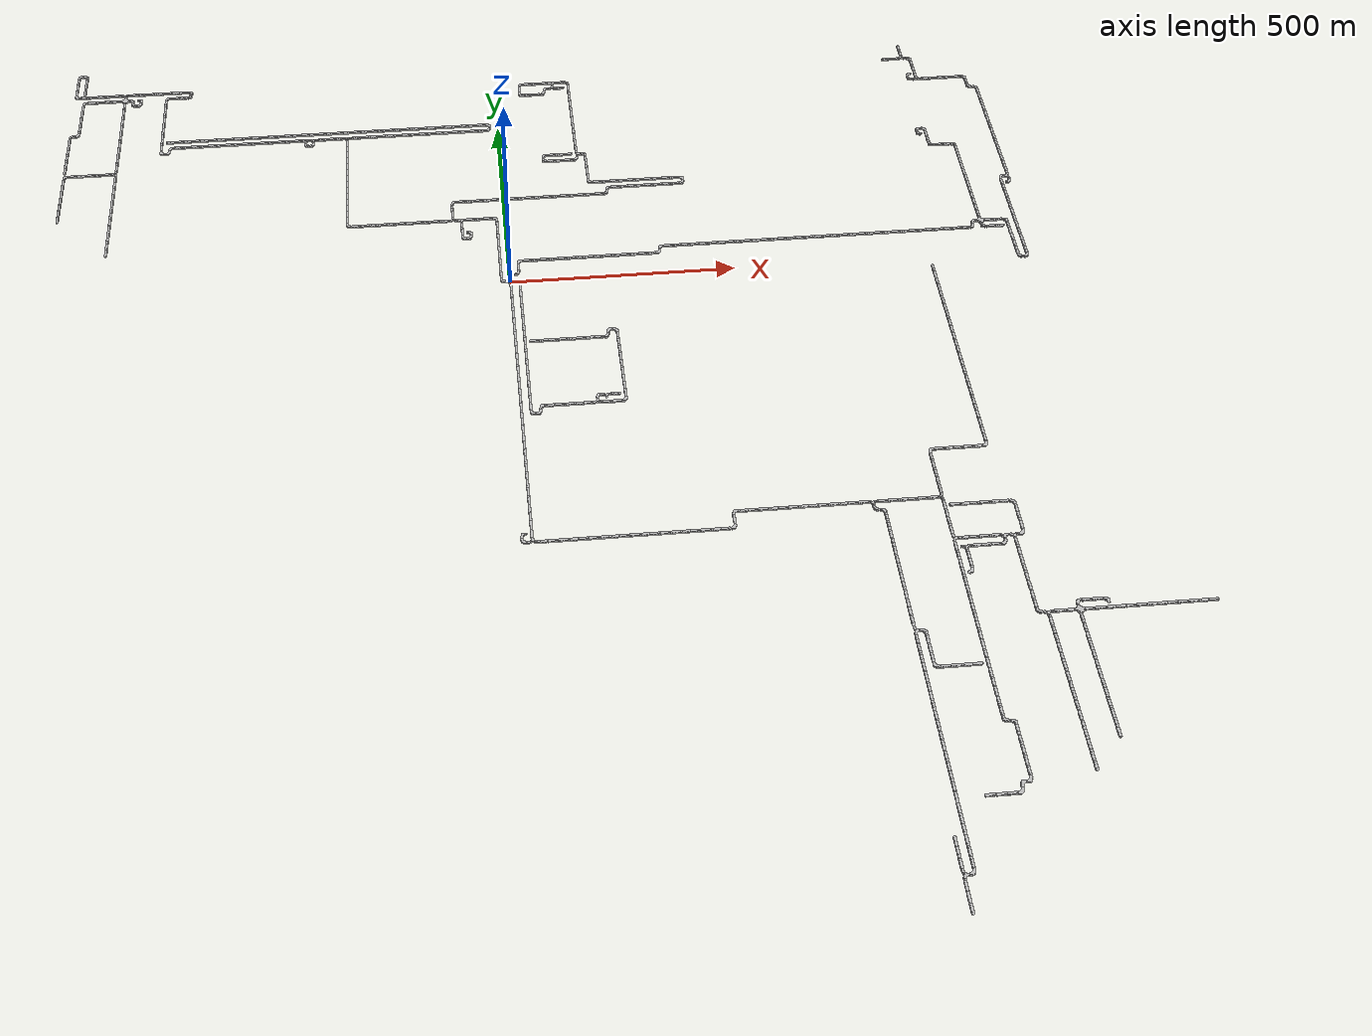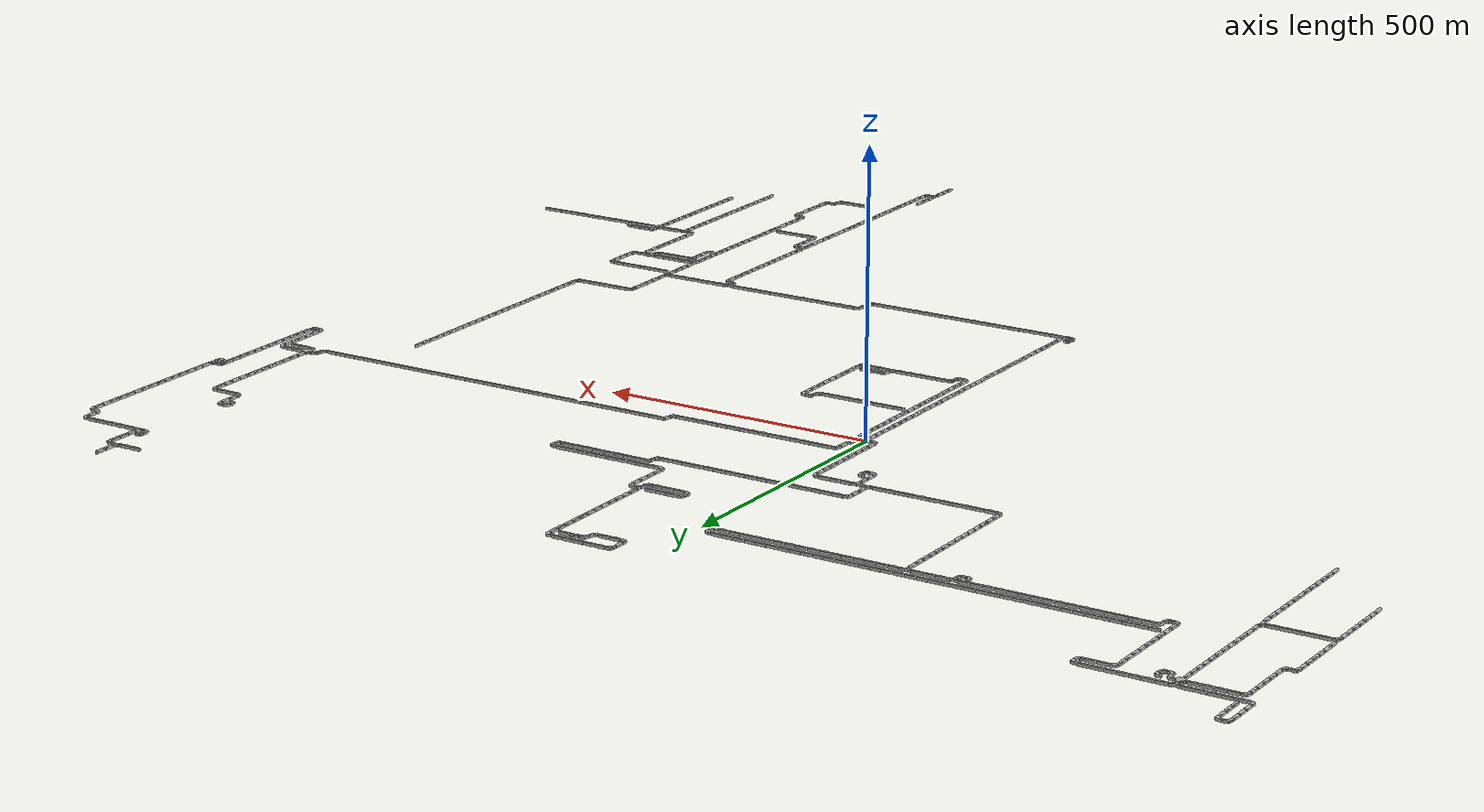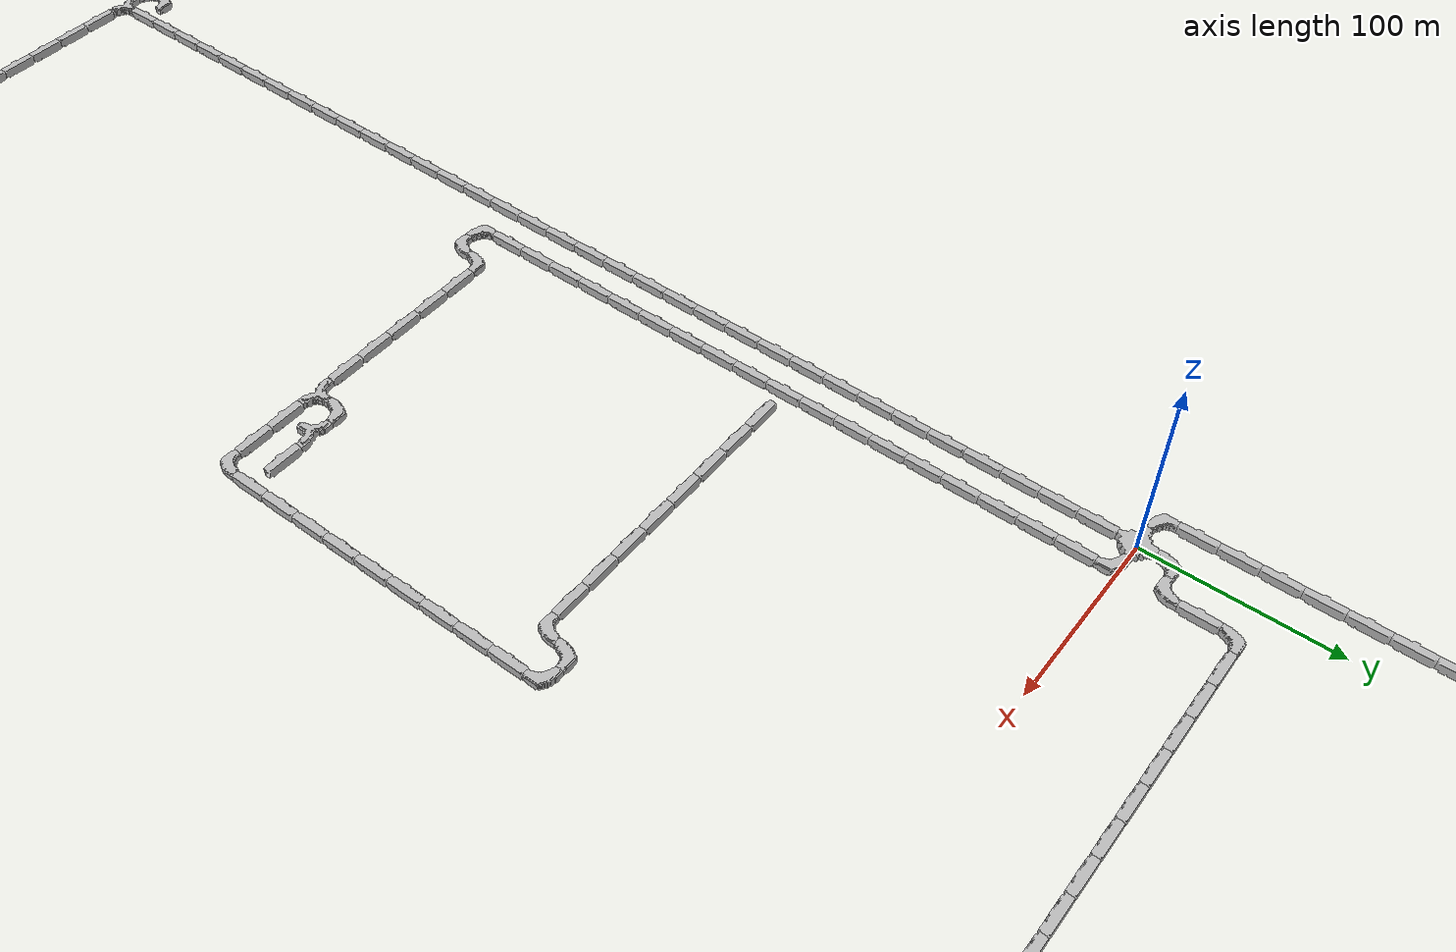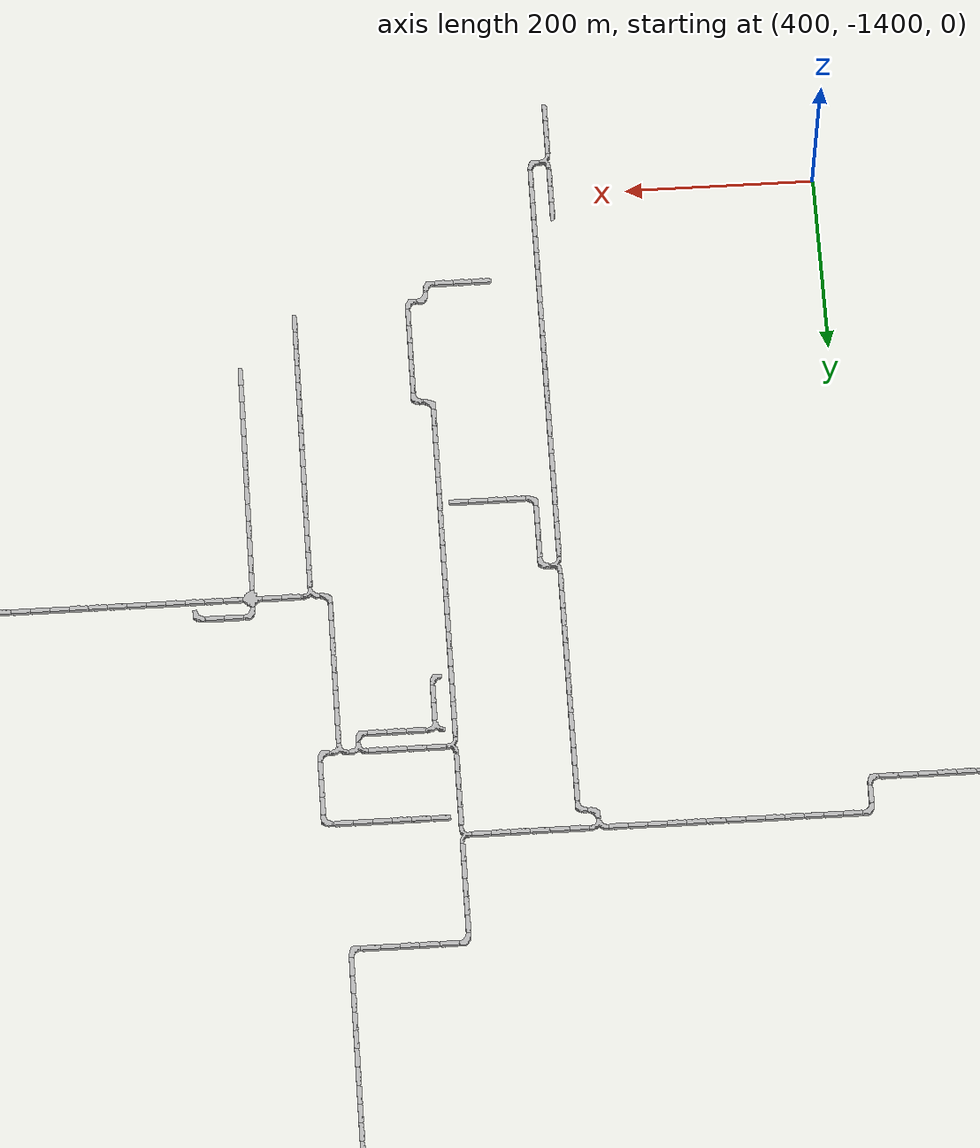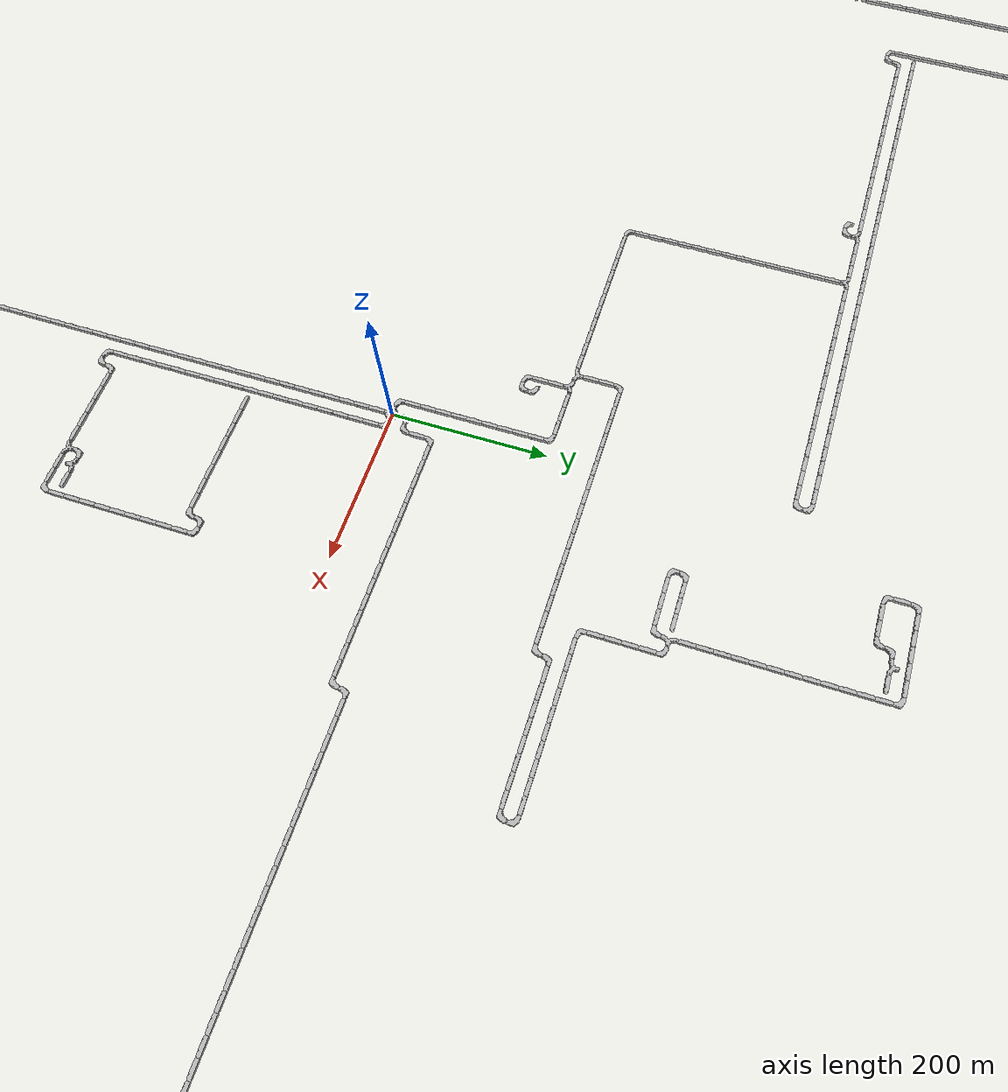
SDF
<sdf version="1.6">
 <world name="cave_16000_8">
  <include>
   <static>true</static>
   <name>cave_0_0</name>
   <pose>0 0 0 0 0 -1.5707963267948966</pose>
   <uri>model://cave_4way_20m</uri>
  </include>
  <include>
   <static>true</static>
   <name>cave_1_0</name>
   <pose>20 0 0 0 0 3.141592653589793</pose>
   <uri>model://cave_L_20m</uri>
  </include>
  <include>
   <static>true</static>
   <name>cave_1_-1</name>
   <pose>20 -20 0 0 0 0.0</pose>
   <uri>model://cave_straight_20m</uri>
  </include>
  <include>
   <static>true</static>
   <name>cave_1_-2</name>
   <pose>20 -40 0 0 0 0.0</pose>
   <uri>model://cave_straight_20m</uri>
  </include>
  <include>
   <static>true</static>
   <name>cave_1_-3</name>
   <pose>20 -60 0 0 0 0.0</pose>
   <uri>model://cave_straight_20m</uri>
  </include>
  <include>
   <static>true</static>
   <name>cave_1_-4</name>
   <pose>20 -80 0 0 0 0.0</pose>
   <uri>model://cave_straight_20m</uri>
  </include>
  <include>
   <static>true</static>
   <name>cave_1_-5</name>
   <pose>20 -100 0 0 0 0.0</pose>
   <uri>model://cave_straight_20m</uri>
  </include>
  <include>
   <static>true</static>
   <name>cave_1_-6</name>
   <pose>20 -120 0 0 0 0.0</pose>
   <uri>model://cave_straight_20m</uri>
  </include>
  <include>
   <static>true</static>
   <name>cave_1_-7</name>
   <pose>20 -140 0 0 0 0.0</pose>
   <uri>model://cave_straight_20m</uri>
  </include>
  <include>
   <static>true</static>
   <name>cave_1_-8</name>
   <pose>20 -160 0 0 0 0.0</pose>
   <uri>model://cave_straight_20m</uri>
  </include>
  <include>
   <static>true</static>
   <name>cave_1_-9</name>
   <pose>20 -180 0 0 0 0.0</pose>
   <uri>model://cave_straight_20m</uri>
  </include>
  <include>
   <static>true</static>
   <name>cave_1_-10</name>
   <pose>20 -200 0 0 0 0.0</pose>
   <uri>model://cave_straight_20m</uri>
  </include>
  <include>
   <static>true</static>
   <name>cave_1_-11</name>
   <pose>20 -220 0 0 0 0.0</pose>
   <uri>model://cave_straight_20m</uri>
  </include>
  <include>
   <static>true</static>
   <name>cave_1_-12</name>
   <pose>20 -240 0 0 0 0.0</pose>
   <uri>model://cave_straight_20m</uri>
  </include>
  <include>
   <static>true</static>
   <name>cave_1_-13</name>
   <pose>20 -260 0 0 0 0.0</pose>
   <uri>model://cave_straight_20m</uri>
  </include>
  <include>
   <static>true</static>
   <name>cave_1_-14</name>
   <pose>20 -280 0 0 0 0.0</pose>
   <uri>model://cave_straight_20m</uri>
  </include>
  <include>
   <static>true</static>
   <name>cave_1_-15</name>
   <pose>20 -300 0 0 0 0.0</pose>
   <uri>model://cave_straight_20m</uri>
  </include>
  <include>
   <static>true</static>
   <name>cave_1_-16</name>
   <pose>20 -320 0 0 0 0.0</pose>
   <uri>model://cave_straight_20m</uri>
  </include>
  <include>
   <static>true</static>
   <name>cave_1_-17</name>
   <pose>20 -340 0 0 0 0.0</pose>
   <uri>model://cave_straight_20m</uri>
  </include>
  <include>
   <static>true</static>
   <name>cave_1_-18</name>
   <pose>20 -360 0 0 0 0.0</pose>
   <uri>model://cave_straight_20m</uri>
  </include>
  <include>
   <static>true</static>
   <name>cave_1_-19</name>
   <pose>20 -380 0 0 0 0.0</pose>
   <uri>model://cave_L_20m</uri>
  </include>
  <include>
   <static>true</static>
   <name>cave_2_-19</name>
   <pose>40 -380 0 0 0 1.5707963267948966</pose>
   <uri>model://cave_L_20m</uri>
  </include>
  <include>
   <static>true</static>
   <name>cave_2_-18</name>
   <pose>40 -360 0 0 0 -1.5707963267948966</pose>
   <uri>model://cave_L_20m</uri>
  </include>
  <include>
   <static>true</static>
   <name>cave_3_-18</name>
   <pose>60 -360 0 0 0 1.5707963267948966</pose>
   <uri>model://cave_straight_20m</uri>
  </include>
  <include>
   <static>true</static>
   <name>cave_4_-18</name>
   <pose>80 -360 0 0 0 1.5707963267948966</pose>
   <uri>model://cave_straight_20m</uri>
  </include>
  <include>
   <static>true</static>
   <name>cave_5_-18</name>
   <pose>100 -360 0 0 0 1.5707963267948966</pose>
   <uri>model://cave_straight_20m</uri>
  </include>
  <include>
   <static>true</static>
   <name>cave_6_-18</name>
   <pose>120 -360 0 0 0 1.5707963267948966</pose>
   <uri>model://cave_straight_20m</uri>
  </include>
  <include>
   <static>true</static>
   <name>cave_7_-18</name>
   <pose>140 -360 0 0 0 1.5707963267948966</pose>
   <uri>model://cave_straight_20m</uri>
  </include>
  <include>
   <static>true</static>
   <name>cave_8_-18</name>
   <pose>160 -360 0 0 0 0.0</pose>
   <uri>model://cave_3way_20m</uri>
  </include>
  <include>
   <static>true</static>
   <name>cave_9_-18</name>
   <pose>180 -360 0 0 0 1.5707963267948966</pose>
   <uri>model://cave_straight_20m</uri>
  </include>
  <include>
   <static>true</static>
   <name>cave_10_-18</name>
   <pose>200 -360 0 0 0 1.5707963267948966</pose>
   <uri>model://cave_straight_20m</uri>
  </include>
  <include>
   <static>true</static>
   <name>cave_11_-18</name>
   <pose>220 -360 0 0 0 1.5707963267948966</pose>
   <uri>model://cave_L_20m</uri>
  </include>
  <include>
   <static>true</static>
   <name>cave_11_-17</name>
   <pose>220 -340 0 0 0 0.0</pose>
   <uri>model://cave_straight_20m</uri>
  </include>
  <include>
   <static>true</static>
   <name>cave_11_-16</name>
   <pose>220 -320 0 0 0 0.0</pose>
   <uri>model://cave_straight_20m</uri>
  </include>
  <include>
   <static>true</static>
   <name>cave_11_-15</name>
   <pose>220 -300 0 0 0 0.0</pose>
   <uri>model://cave_straight_20m</uri>
  </include>
  <include>
   <static>true</static>
   <name>cave_11_-14</name>
   <pose>220 -280 0 0 0 0.0</pose>
   <uri>model://cave_straight_20m</uri>
  </include>
  <include>
   <static>true</static>
   <name>cave_11_-13</name>
   <pose>220 -260 0 0 0 0.0</pose>
   <uri>model://cave_straight_20m</uri>
  </include>
  <include>
   <static>true</static>
   <name>cave_11_-12</name>
   <pose>220 -240 0 0 0 0.0</pose>
   <uri>model://cave_straight_20m</uri>
  </include>
  <include>
   <static>true</static>
   <name>cave_11_-11</name>
   <pose>220 -220 0 0 0 0.0</pose>
   <uri>model://cave_straight_20m</uri>
  </include>
  <include>
   <static>true</static>
   <name>cave_11_-10</name>
   <pose>220 -200 0 0 0 0.0</pose>
   <uri>model://cave_straight_20m</uri>
  </include>
  <include>
   <static>true</static>
   <name>cave_11_-9</name>
   <pose>220 -180 0 0 0 0.0</pose>
   <uri>model://cave_straight_20m</uri>
  </include>
  <include>
   <static>true</static>
   <name>cave_11_-8</name>
   <pose>220 -160 0 0 0 3.141592653589793</pose>
   <uri>model://cave_L_20m</uri>
  </include>
  <include>
   <static>true</static>
   <name>cave_10_-8</name>
   <pose>200 -160 0 0 0 -1.5707963267948966</pose>
   <uri>model://cave_L_20m</uri>
  </include>
  <include>
   <static>true</static>
   <name>cave_10_-9</name>
   <pose>200 -180 0 0 0 1.5707963267948966</pose>
   <uri>model://cave_L_20m</uri>
  </include>
  <include>
   <static>true</static>
   <name>cave_9_-9</name>
   <pose>180 -180 0 0 0 1.5707963267948966</pose>
   <uri>model://cave_straight_20m</uri>
  </include>
  <include>
   <static>true</static>
   <name>cave_8_-9</name>
   <pose>160 -180 0 0 0 1.5707963267948966</pose>
   <uri>model://cave_straight_20m</uri>
  </include>
  <include>
   <static>true</static>
   <name>cave_7_-9</name>
   <pose>140 -180 0 0 0 1.5707963267948966</pose>
   <uri>model://cave_straight_20m</uri>
  </include>
  <include>
   <static>true</static>
   <name>cave_6_-9</name>
   <pose>120 -180 0 0 0 1.5707963267948966</pose>
   <uri>model://cave_straight_20m</uri>
  </include>
  <include>
   <static>true</static>
   <name>cave_5_-9</name>
   <pose>100 -180 0 0 0 1.5707963267948966</pose>
   <uri>model://cave_straight_20m</uri>
  </include>
  <include>
   <static>true</static>
   <name>cave_4_-9</name>
   <pose>80 -180 0 0 0 1.5707963267948966</pose>
   <uri>model://cave_straight_20m</uri>
  </include>
  <include>
   <static>true</static>
   <name>cave_3_-9</name>
   <pose>60 -180 0 0 0 1.5707963267948966</pose>
   <uri>model://cave_straight_20m</uri>
  </include>
  <include>
   <static>true</static>
   <name>cave_2_-9</name>
   <pose>40 -180 0 0 0 1.5707963267948966</pose>
   <uri>model://cave_straight_20m</uri>
  </include>
  <include>
   <static>true</static>
   <name>cave_8_-17</name>
   <pose>160 -340 0 0 0 -1.5707963267948966</pose>
   <uri>model://cave_L_20m</uri>
  </include>
  <include>
   <static>true</static>
   <name>cave_9_-17</name>
   <pose>180 -340 0 0 0 3.141592653589793</pose>
   <uri>model://cave_3way_20m</uri>
  </include>
  <include>
   <static>true</static>
   <name>cave_10_-17</name>
   <pose>200 -340 0 0 0 1.5707963267948966</pose>
   <uri>model://cave_straight_20m</uri>
  </include>
  <include>
   <static>true</static>
   <name>cave_0_-1</name>
   <pose>0 -20 0 0 0 0.0</pose>
   <uri>model://cave_straight_20m</uri>
  </include>
  <include>
   <static>true</static>
   <name>cave_0_-2</name>
   <pose>0 -40 0 0 0 0.0</pose>
   <uri>model://cave_straight_20m</uri>
  </include>
  <include>
   <static>true</static>
   <name>cave_0_-3</name>
   <pose>0 -60 0 0 0 0.0</pose>
   <uri>model://cave_straight_20m</uri>
  </include>
  <include>
   <static>true</static>
   <name>cave_0_-4</name>
   <pose>0 -80 0 0 0 0.0</pose>
   <uri>model://cave_straight_20m</uri>
  </include>
  <include>
   <static>true</static>
   <name>cave_0_-5</name>
   <pose>0 -100 0 0 0 0.0</pose>
   <uri>model://cave_straight_20m</uri>
  </include>
  <include>
   <static>true</static>
   <name>cave_0_-6</name>
   <pose>0 -120 0 0 0 0.0</pose>
   <uri>model://cave_straight_20m</uri>
  </include>
  <include>
   <static>true</static>
   <name>cave_0_-7</name>
   <pose>0 -140 0 0 0 0.0</pose>
   <uri>model://cave_straight_20m</uri>
  </include>
  <include>
   <static>true</static>
   <name>cave_0_-8</name>
   <pose>0 -160 0 0 0 0.0</pose>
   <uri>model://cave_straight_20m</uri>
  </include>
  <include>
   <static>true</static>
   <name>cave_0_-9</name>
   <pose>0 -180 0 0 0 0.0</pose>
   <uri>model://cave_straight_20m</uri>
  </include>
  <include>
   <static>true</static>
   <name>cave_0_-10</name>
   <pose>0 -200 0 0 0 0.0</pose>
   <uri>model://cave_straight_20m</uri>
  </include>
  <include>
   <static>true</static>
   <name>cave_0_-11</name>
   <pose>0 -220 0 0 0 0.0</pose>
   <uri>model://cave_straight_20m</uri>
  </include>
  <include>
   <static>true</static>
   <name>cave_0_-12</name>
   <pose>0 -240 0 0 0 0.0</pose>
   <uri>model://cave_straight_20m</uri>
  </include>
  <include>
   <static>true</static>
   <name>cave_0_-13</name>
   <pose>0 -260 0 0 0 0.0</pose>
   <uri>model://cave_straight_20m</uri>
  </include>
  <include>
   <static>true</static>
   <name>cave_0_-14</name>
   <pose>0 -280 0 0 0 0.0</pose>
   <uri>model://cave_straight_20m</uri>
  </include>
  <include>
   <static>true</static>
   <name>cave_0_-15</name>
   <pose>0 -300 0 0 0 0.0</pose>
   <uri>model://cave_straight_20m</uri>
  </include>
  <include>
   <static>true</static>
   <name>cave_0_-16</name>
   <pose>0 -320 0 0 0 0.0</pose>
   <uri>model://cave_straight_20m</uri>
  </include>
  <include>
   <static>true</static>
   <name>cave_0_-17</name>
   <pose>0 -340 0 0 0 0.0</pose>
   <uri>model://cave_straight_20m</uri>
  </include>
  <include>
   <static>true</static>
   <name>cave_0_-18</name>
   <pose>0 -360 0 0 0 0.0</pose>
   <uri>model://cave_straight_20m</uri>
  </include>
  <include>
   <static>true</static>
   <name>cave_0_-19</name>
   <pose>0 -380 0 0 0 0.0</pose>
   <uri>model://cave_straight_20m</uri>
  </include>
  <include>
   <static>true</static>
   <name>cave_0_-20</name>
   <pose>0 -400 0 0 0 0.0</pose>
   <uri>model://cave_straight_20m</uri>
  </include>
  <include>
   <static>true</static>
   <name>cave_0_-21</name>
   <pose>0 -420 0 0 0 0.0</pose>
   <uri>model://cave_straight_20m</uri>
  </include>
  <include>
   <static>true</static>
   <name>cave_0_-22</name>
   <pose>0 -440 0 0 0 0.0</pose>
   <uri>model://cave_straight_20m</uri>
  </include>
  <include>
   <static>true</static>
   <name>cave_0_-23</name>
   <pose>0 -460 0 0 0 0.0</pose>
   <uri>model://cave_straight_20m</uri>
  </include>
  <include>
   <static>true</static>
   <name>cave_0_-24</name>
   <pose>0 -480 0 0 0 0.0</pose>
   <uri>model://cave_straight_20m</uri>
  </include>
  <include>
   <static>true</static>
   <name>cave_0_-25</name>
   <pose>0 -500 0 0 0 0.0</pose>
   <uri>model://cave_straight_20m</uri>
  </include>
  <include>
   <static>true</static>
   <name>cave_0_-26</name>
   <pose>0 -520 0 0 0 0.0</pose>
   <uri>model://cave_straight_20m</uri>
  </include>
  <include>
   <static>true</static>
   <name>cave_0_-27</name>
   <pose>0 -540 0 0 0 0.0</pose>
   <uri>model://cave_straight_20m</uri>
  </include>
  <include>
   <static>true</static>
   <name>cave_0_-28</name>
   <pose>0 -560 0 0 0 0.0</pose>
   <uri>model://cave_straight_20m</uri>
  </include>
  <include>
   <static>true</static>
   <name>cave_0_-29</name>
   <pose>0 -580 0 0 0 0.0</pose>
   <uri>model://cave_straight_20m</uri>
  </include>
  <include>
   <static>true</static>
   <name>cave_0_-30</name>
   <pose>0 -600 0 0 0 0.0</pose>
   <uri>model://cave_straight_20m</uri>
  </include>
  <include>
   <static>true</static>
   <name>cave_0_-31</name>
   <pose>0 -620 0 0 0 0.0</pose>
   <uri>model://cave_straight_20m</uri>
  </include>
  <include>
   <static>true</static>
   <name>cave_0_-32</name>
   <pose>0 -640 0 0 0 0.0</pose>
   <uri>model://cave_straight_20m</uri>
  </include>
  <include>
   <static>true</static>
   <name>cave_0_-33</name>
   <pose>0 -660 0 0 0 0.0</pose>
   <uri>model://cave_straight_20m</uri>
  </include>
  <include>
   <static>true</static>
   <name>cave_0_-34</name>
   <pose>0 -680 0 0 0 0.0</pose>
   <uri>model://cave_straight_20m</uri>
  </include>
  <include>
   <static>true</static>
   <name>cave_0_-35</name>
   <pose>0 -700 0 0 0 0.0</pose>
   <uri>model://cave_3way_20m</uri>
  </include>
  <include>
   <static>true</static>
   <name>cave_1_-35</name>
   <pose>20 -700 0 0 0 1.5707963267948966</pose>
   <uri>model://cave_straight_20m</uri>
  </include>
  <include>
   <static>true</static>
   <name>cave_2_-35</name>
   <pose>40 -700 0 0 0 1.5707963267948966</pose>
   <uri>model://cave_straight_20m</uri>
  </include>
  <include>
   <static>true</static>
   <name>cave_3_-35</name>
   <pose>60 -700 0 0 0 1.5707963267948966</pose>
   <uri>model://cave_straight_20m</uri>
  </include>
  <include>
   <static>true</static>
   <name>cave_4_-35</name>
   <pose>80 -700 0 0 0 1.5707963267948966</pose>
   <uri>model://cave_straight_20m</uri>
  </include>
  <include>
   <static>true</static>
   <name>cave_5_-35</name>
   <pose>100 -700 0 0 0 1.5707963267948966</pose>
   <uri>model://cave_straight_20m</uri>
  </include>
  <include>
   <static>true</static>
   <name>cave_6_-35</name>
   <pose>120 -700 0 0 0 1.5707963267948966</pose>
   <uri>model://cave_straight_20m</uri>
  </include>
  <include>
   <static>true</static>
   <name>cave_7_-35</name>
   <pose>140 -700 0 0 0 1.5707963267948966</pose>
   <uri>model://cave_straight_20m</uri>
  </include>
  <include>
   <static>true</static>
   <name>cave_8_-35</name>
   <pose>160 -700 0 0 0 1.5707963267948966</pose>
   <uri>model://cave_straight_20m</uri>
  </include>
  <include>
   <static>true</static>
   <name>cave_9_-35</name>
   <pose>180 -700 0 0 0 1.5707963267948966</pose>
   <uri>model://cave_straight_20m</uri>
  </include>
  <include>
   <static>true</static>
   <name>cave_10_-35</name>
   <pose>200 -700 0 0 0 1.5707963267948966</pose>
   <uri>model://cave_straight_20m</uri>
  </include>
  <include>
   <static>true</static>
   <name>cave_11_-35</name>
   <pose>220 -700 0 0 0 1.5707963267948966</pose>
   <uri>model://cave_straight_20m</uri>
  </include>
  <include>
   <static>true</static>
   <name>cave_12_-35</name>
   <pose>240 -700 0 0 0 1.5707963267948966</pose>
   <uri>model://cave_straight_20m</uri>
  </include>
  <include>
   <static>true</static>
   <name>cave_13_-35</name>
   <pose>260 -700 0 0 0 1.5707963267948966</pose>
   <uri>model://cave_straight_20m</uri>
  </include>
  <include>
   <static>true</static>
   <name>cave_14_-35</name>
   <pose>280 -700 0 0 0 1.5707963267948966</pose>
   <uri>model://cave_straight_20m</uri>
  </include>
  <include>
   <static>true</static>
   <name>cave_15_-35</name>
   <pose>300 -700 0 0 0 1.5707963267948966</pose>
   <uri>model://cave_straight_20m</uri>
  </include>
  <include>
   <static>true</static>
   <name>cave_16_-35</name>
   <pose>320 -700 0 0 0 1.5707963267948966</pose>
   <uri>model://cave_straight_20m</uri>
  </include>
  <include>
   <static>true</static>
   <name>cave_17_-35</name>
   <pose>340 -700 0 0 0 1.5707963267948966</pose>
   <uri>model://cave_straight_20m</uri>
  </include>
  <include>
   <static>true</static>
   <name>cave_18_-35</name>
   <pose>360 -700 0 0 0 1.5707963267948966</pose>
   <uri>model://cave_straight_20m</uri>
  </include>
  <include>
   <static>true</static>
   <name>cave_19_-35</name>
   <pose>380 -700 0 0 0 1.5707963267948966</pose>
   <uri>model://cave_straight_20m</uri>
  </include>
  <include>
   <static>true</static>
   <name>cave_20_-35</name>
   <pose>400 -700 0 0 0 1.5707963267948966</pose>
   <uri>model://cave_L_20m</uri>
  </include>
  <include>
   <static>true</static>
   <name>cave_20_-34</name>
   <pose>400 -680 0 0 0 0.0</pose>
   <uri>model://cave_straight_20m</uri>
  </include>
  <include>
   <static>true</static>
   <name>cave_20_-33</name>
   <pose>400 -660 0 0 0 -1.5707963267948966</pose>
   <uri>model://cave_L_20m</uri>
  </include>
  <include>
   <static>true</static>
   <name>cave_21_-33</name>
   <pose>420 -660 0 0 0 1.5707963267948966</pose>
   <uri>model://cave_straight_20m</uri>
  </include>
  <include>
   <static>true</static>
   <name>cave_22_-33</name>
   <pose>440 -660 0 0 0 1.5707963267948966</pose>
   <uri>model://cave_straight_20m</uri>
  </include>
  <include>
   <static>true</static>
   <name>cave_23_-33</name>
   <pose>460 -660 0 0 0 1.5707963267948966</pose>
   <uri>model://cave_straight_20m</uri>
  </include>
  <include>
   <static>true</static>
   <name>cave_24_-33</name>
   <pose>480 -660 0 0 0 1.5707963267948966</pose>
   <uri>model://cave_straight_20m</uri>
  </include>
  <include>
   <static>true</static>
   <name>cave_25_-33</name>
   <pose>500 -660 0 0 0 1.5707963267948966</pose>
   <uri>model://cave_straight_20m</uri>
  </include>
  <include>
   <static>true</static>
   <name>cave_26_-33</name>
   <pose>520 -660 0 0 0 1.5707963267948966</pose>
   <uri>model://cave_straight_20m</uri>
  </include>
  <include>
   <static>true</static>
   <name>cave_27_-33</name>
   <pose>540 -660 0 0 0 1.5707963267948966</pose>
   <uri>model://cave_straight_20m</uri>
  </include>
  <include>
   <static>true</static>
   <name>cave_28_-33</name>
   <pose>560 -660 0 0 0 1.5707963267948966</pose>
   <uri>model://cave_straight_20m</uri>
  </include>
  <include>
   <static>true</static>
   <name>cave_29_-33</name>
   <pose>580 -660 0 0 0 1.5707963267948966</pose>
   <uri>model://cave_straight_20m</uri>
  </include>
  <include>
   <static>true</static>
   <name>cave_30_-33</name>
   <pose>600 -660 0 0 0 1.5707963267948966</pose>
   <uri>model://cave_straight_20m</uri>
  </include>
  <include>
   <static>true</static>
   <name>cave_31_-33</name>
   <pose>620 -660 0 0 0 1.5707963267948966</pose>
   <uri>model://cave_straight_20m</uri>
  </include>
  <include>
   <static>true</static>
   <name>cave_32_-33</name>
   <pose>640 -660 0 0 0 1.5707963267948966</pose>
   <uri>model://cave_straight_20m</uri>
  </include>
  <include>
   <static>true</static>
   <name>cave_33_-33</name>
   <pose>660 -660 0 0 0 1.5707963267948966</pose>
   <uri>model://cave_straight_20m</uri>
  </include>
  <include>
   <static>true</static>
   <name>cave_34_-33</name>
   <pose>680 -660 0 0 0 3.141592653589793</pose>
   <uri>model://cave_3way_20m</uri>
  </include>
  <include>
   <static>true</static>
   <name>cave_35_-33</name>
   <pose>700 -660 0 0 0 1.5707963267948966</pose>
   <uri>model://cave_straight_20m</uri>
  </include>
  <include>
   <static>true</static>
   <name>cave_36_-33</name>
   <pose>720 -660 0 0 0 1.5707963267948966</pose>
   <uri>model://cave_straight_20m</uri>
  </include>
  <include>
   <static>true</static>
   <name>cave_37_-33</name>
   <pose>740 -660 0 0 0 1.5707963267948966</pose>
   <uri>model://cave_straight_20m</uri>
  </include>
  <include>
   <static>true</static>
   <name>cave_38_-33</name>
   <pose>760 -660 0 0 0 1.5707963267948966</pose>
   <uri>model://cave_straight_20m</uri>
  </include>
  <include>
   <static>true</static>
   <name>cave_39_-33</name>
   <pose>780 -660 0 0 0 1.5707963267948966</pose>
   <uri>model://cave_straight_20m</uri>
  </include>
  <include>
   <static>true</static>
   <name>cave_40_-33</name>
   <pose>800 -660 0 0 0 1.5707963267948966</pose>
   <uri>model://cave_straight_20m</uri>
  </include>
  <include>
   <static>true</static>
   <name>cave_41_-33</name>
   <pose>820 -660 0 0 0 1.5707963267948966</pose>
   <uri>model://cave_3way_20m</uri>
  </include>
  <include>
   <static>true</static>
   <name>cave_41_-34</name>
   <pose>820 -680 0 0 0 0.0</pose>
   <uri>model://cave_straight_20m</uri>
  </include>
  <include>
   <static>true</static>
   <name>cave_41_-35</name>
   <pose>820 -700 0 0 0 0.0</pose>
   <uri>model://cave_straight_20m</uri>
  </include>
  <include>
   <static>true</static>
   <name>cave_41_-36</name>
   <pose>820 -720 0 0 0 0.0</pose>
   <uri>model://cave_straight_20m</uri>
  </include>
  <include>
   <static>true</static>
   <name>cave_41_-37</name>
   <pose>820 -740 0 0 0 0.0</pose>
   <uri>model://cave_straight_20m</uri>
  </include>
  <include>
   <static>true</static>
   <name>cave_41_-38</name>
   <pose>820 -760 0 0 0 -1.5707963267948966</pose>
   <uri>model://cave_3way_20m</uri>
  </include>
  <include>
   <static>true</static>
   <name>cave_42_-38</name>
   <pose>840 -760 0 0 0 1.5707963267948966</pose>
   <uri>model://cave_straight_20m</uri>
  </include>
  <include>
   <static>true</static>
   <name>cave_43_-38</name>
   <pose>860 -760 0 0 0 1.5707963267948966</pose>
   <uri>model://cave_straight_20m</uri>
  </include>
  <include>
   <static>true</static>
   <name>cave_44_-38</name>
   <pose>880 -760 0 0 0 1.5707963267948966</pose>
   <uri>model://cave_straight_20m</uri>
  </include>
  <include>
   <static>true</static>
   <name>cave_45_-38</name>
   <pose>900 -760 0 0 0 1.5707963267948966</pose>
   <uri>model://cave_straight_20m</uri>
  </include>
  <include>
   <static>true</static>
   <name>cave_46_-38</name>
   <pose>920 -760 0 0 0 3.141592653589793</pose>
   <uri>model://cave_3way_20m</uri>
  </include>
  <include>
   <static>true</static>
   <name>cave_47_-38</name>
   <pose>940 -760 0 0 0 3.141592653589793</pose>
   <uri>model://cave_3way_20m</uri>
  </include>
  <include>
   <static>true</static>
   <name>cave_48_-38</name>
   <pose>960 -760 0 0 0 1.5707963267948966</pose>
   <uri>model://cave_L_20m</uri>
  </include>
  <include>
   <static>true</static>
   <name>cave_48_-37</name>
   <pose>960 -740 0 0 0 0.0</pose>
   <uri>model://cave_straight_20m</uri>
  </include>
  <include>
   <static>true</static>
   <name>cave_48_-36</name>
   <pose>960 -720 0 0 0 0.0</pose>
   <uri>model://cave_straight_20m</uri>
  </include>
  <include>
   <static>true</static>
   <name>cave_48_-35</name>
   <pose>960 -700 0 0 0 0.0</pose>
   <uri>model://cave_straight_20m</uri>
  </include>
  <include>
   <static>true</static>
   <name>cave_48_-34</name>
   <pose>960 -680 0 0 0 3.141592653589793</pose>
   <uri>model://cave_L_20m</uri>
  </include>
  <include>
   <static>true</static>
   <name>cave_47_-34</name>
   <pose>940 -680 0 0 0 1.5707963267948966</pose>
   <uri>model://cave_straight_20m</uri>
  </include>
  <include>
   <static>true</static>
   <name>cave_46_-34</name>
   <pose>920 -680 0 0 0 1.5707963267948966</pose>
   <uri>model://cave_straight_20m</uri>
  </include>
  <include>
   <static>true</static>
   <name>cave_45_-34</name>
   <pose>900 -680 0 0 0 1.5707963267948966</pose>
   <uri>model://cave_straight_20m</uri>
  </include>
  <include>
   <static>true</static>
   <name>cave_44_-34</name>
   <pose>880 -680 0 0 0 1.5707963267948966</pose>
   <uri>model://cave_straight_20m</uri>
  </include>
  <include>
   <static>true</static>
   <name>cave_43_-34</name>
   <pose>860 -680 0 0 0 1.5707963267948966</pose>
   <uri>model://cave_straight_20m</uri>
  </include>
  <include>
   <static>true</static>
   <name>cave_42_-34</name>
   <pose>840 -680 0 0 0 1.5707963267948966</pose>
   <uri>model://cave_straight_20m</uri>
  </include>
  <include>
   <static>true</static>
   <name>cave_47_-39</name>
   <pose>940 -780 0 0 0 0.0</pose>
   <uri>model://cave_straight_20m</uri>
  </include>
  <include>
   <static>true</static>
   <name>cave_47_-40</name>
   <pose>940 -800 0 0 0 0.0</pose>
   <uri>model://cave_straight_20m</uri>
  </include>
  <include>
   <static>true</static>
   <name>cave_47_-41</name>
   <pose>940 -820 0 0 0 0.0</pose>
   <uri>model://cave_straight_20m</uri>
  </include>
  <include>
   <static>true</static>
   <name>cave_47_-42</name>
   <pose>940 -840 0 0 0 0.0</pose>
   <uri>model://cave_straight_20m</uri>
  </include>
  <include>
   <static>true</static>
   <name>cave_47_-43</name>
   <pose>940 -860 0 0 0 0.0</pose>
   <uri>model://cave_straight_20m</uri>
  </include>
  <include>
   <static>true</static>
   <name>cave_47_-44</name>
   <pose>940 -880 0 0 0 0.0</pose>
   <uri>model://cave_straight_20m</uri>
  </include>
  <include>
   <static>true</static>
   <name>cave_47_-45</name>
   <pose>940 -900 0 0 0 0.0</pose>
   <uri>model://cave_straight_20m</uri>
  </include>
  <include>
   <static>true</static>
   <name>cave_47_-46</name>
   <pose>940 -920 0 0 0 0.0</pose>
   <uri>model://cave_straight_20m</uri>
  </include>
  <include>
   <static>true</static>
   <name>cave_47_-47</name>
   <pose>940 -940 0 0 0 0.0</pose>
   <uri>model://cave_L_20m</uri>
  </include>
  <include>
   <static>true</static>
   <name>cave_48_-47</name>
   <pose>960 -940 0 0 0 3.141592653589793</pose>
   <uri>model://cave_3way_20m</uri>
  </include>
  <include>
   <static>true</static>
   <name>cave_49_-47</name>
   <pose>980 -940 0 0 0 1.5707963267948966</pose>
   <uri>model://cave_straight_20m</uri>
  </include>
  <include>
   <static>true</static>
   <name>cave_50_-47</name>
   <pose>1000 -940 0 0 0 1.5707963267948966</pose>
   <uri>model://cave_straight_20m</uri>
  </include>
  <include>
   <static>true</static>
   <name>cave_51_-47</name>
   <pose>1020 -940 0 0 0 -1.5707963267948966</pose>
   <uri>model://cave_4way_20m</uri>
  </include>
  <include>
   <static>true</static>
   <name>cave_52_-47</name>
   <pose>1040 -940 0 0 0 1.5707963267948966</pose>
   <uri>model://cave_straight_20m</uri>
  </include>
  <include>
   <static>true</static>
   <name>cave_53_-47</name>
   <pose>1060 -940 0 0 0 1.5707963267948966</pose>
   <uri>model://cave_straight_20m</uri>
  </include>
  <include>
   <static>true</static>
   <name>cave_54_-47</name>
   <pose>1080 -940 0 0 0 1.5707963267948966</pose>
   <uri>model://cave_straight_20m</uri>
  </include>
  <include>
   <static>true</static>
   <name>cave_55_-47</name>
   <pose>1100 -940 0 0 0 1.5707963267948966</pose>
   <uri>model://cave_straight_20m</uri>
  </include>
  <include>
   <static>true</static>
   <name>cave_56_-47</name>
   <pose>1120 -940 0 0 0 1.5707963267948966</pose>
   <uri>model://cave_straight_20m</uri>
  </include>
  <include>
   <static>true</static>
   <name>cave_57_-47</name>
   <pose>1140 -940 0 0 0 1.5707963267948966</pose>
   <uri>model://cave_straight_20m</uri>
  </include>
  <include>
   <static>true</static>
   <name>cave_58_-47</name>
   <pose>1160 -940 0 0 0 1.5707963267948966</pose>
   <uri>model://cave_straight_20m</uri>
  </include>
  <include>
   <static>true</static>
   <name>cave_59_-47</name>
   <pose>1180 -940 0 0 0 1.5707963267948966</pose>
   <uri>model://cave_straight_20m</uri>
  </include>
  <include>
   <static>true</static>
   <name>cave_60_-47</name>
   <pose>1200 -940 0 0 0 1.5707963267948966</pose>
   <uri>model://cave_straight_20m</uri>
  </include>
  <include>
   <static>true</static>
   <name>cave_61_-47</name>
   <pose>1220 -940 0 0 0 1.5707963267948966</pose>
   <uri>model://cave_straight_20m</uri>
  </include>
  <include>
   <static>true</static>
   <name>cave_62_-47</name>
   <pose>1240 -940 0 0 0 1.5707963267948966</pose>
   <uri>model://cave_straight_20m</uri>
  </include>
  <include>
   <static>true</static>
   <name>cave_63_-47</name>
   <pose>1260 -940 0 0 0 1.5707963267948966</pose>
   <uri>model://cave_straight_20m</uri>
  </include>
  <include>
   <static>true</static>
   <name>cave_64_-47</name>
   <pose>1280 -940 0 0 0 1.5707963267948966</pose>
   <uri>model://cave_straight_20m</uri>
  </include>
  <include>
   <static>true</static>
   <name>cave_51_-48</name>
   <pose>1020 -960 0 0 0 0.0</pose>
   <uri>model://cave_straight_20m</uri>
  </include>
  <include>
   <static>true</static>
   <name>cave_51_-49</name>
   <pose>1020 -980 0 0 0 0.0</pose>
   <uri>model://cave_straight_20m</uri>
  </include>
  <include>
   <static>true</static>
   <name>cave_51_-50</name>
   <pose>1020 -1000 0 0 0 0.0</pose>
   <uri>model://cave_straight_20m</uri>
  </include>
  <include>
   <static>true</static>
   <name>cave_51_-51</name>
   <pose>1020 -1020 0 0 0 0.0</pose>
   <uri>model://cave_straight_20m</uri>
  </include>
  <include>
   <static>true</static>
   <name>cave_51_-52</name>
   <pose>1020 -1040 0 0 0 0.0</pose>
   <uri>model://cave_straight_20m</uri>
  </include>
  <include>
   <static>true</static>
   <name>cave_51_-53</name>
   <pose>1020 -1060 0 0 0 0.0</pose>
   <uri>model://cave_straight_20m</uri>
  </include>
  <include>
   <static>true</static>
   <name>cave_51_-54</name>
   <pose>1020 -1080 0 0 0 0.0</pose>
   <uri>model://cave_straight_20m</uri>
  </include>
  <include>
   <static>true</static>
   <name>cave_51_-55</name>
   <pose>1020 -1100 0 0 0 0.0</pose>
   <uri>model://cave_straight_20m</uri>
  </include>
  <include>
   <static>true</static>
   <name>cave_51_-56</name>
   <pose>1020 -1120 0 0 0 0.0</pose>
   <uri>model://cave_straight_20m</uri>
  </include>
  <include>
   <static>true</static>
   <name>cave_51_-57</name>
   <pose>1020 -1140 0 0 0 0.0</pose>
   <uri>model://cave_straight_20m</uri>
  </include>
  <include>
   <static>true</static>
   <name>cave_51_-58</name>
   <pose>1020 -1160 0 0 0 0.0</pose>
   <uri>model://cave_straight_20m</uri>
  </include>
  <include>
   <static>true</static>
   <name>cave_51_-59</name>
   <pose>1020 -1180 0 0 0 0.0</pose>
   <uri>model://cave_straight_20m</uri>
  </include>
  <include>
   <static>true</static>
   <name>cave_51_-60</name>
   <pose>1020 -1200 0 0 0 0.0</pose>
   <uri>model://cave_straight_20m</uri>
  </include>
  <include>
   <static>true</static>
   <name>cave_51_-46</name>
   <pose>1020 -920 0 0 0 -1.5707963267948966</pose>
   <uri>model://cave_L_20m</uri>
  </include>
  <include>
   <static>true</static>
   <name>cave_52_-46</name>
   <pose>1040 -920 0 0 0 1.5707963267948966</pose>
   <uri>model://cave_straight_20m</uri>
  </include>
  <include>
   <static>true</static>
   <name>cave_53_-46</name>
   <pose>1060 -920 0 0 0 1.5707963267948966</pose>
   <uri>model://cave_straight_20m</uri>
  </include>
  <include>
   <static>true</static>
   <name>cave_54_-46</name>
   <pose>1080 -920 0 0 0 3.141592653589793</pose>
   <uri>model://cave_L_20m</uri>
  </include>
  <include>
   <static>true</static>
   <name>cave_48_-48</name>
   <pose>960 -960 0 0 0 0.0</pose>
   <uri>model://cave_straight_20m</uri>
  </include>
  <include>
   <static>true</static>
   <name>cave_48_-49</name>
   <pose>960 -980 0 0 0 0.0</pose>
   <uri>model://cave_straight_20m</uri>
  </include>
  <include>
   <static>true</static>
   <name>cave_48_-50</name>
   <pose>960 -1000 0 0 0 0.0</pose>
   <uri>model://cave_straight_20m</uri>
  </include>
  <include>
   <static>true</static>
   <name>cave_48_-51</name>
   <pose>960 -1020 0 0 0 0.0</pose>
   <uri>model://cave_straight_20m</uri>
  </include>
  <include>
   <static>true</static>
   <name>cave_48_-52</name>
   <pose>960 -1040 0 0 0 0.0</pose>
   <uri>model://cave_straight_20m</uri>
  </include>
  <include>
   <static>true</static>
   <name>cave_48_-53</name>
   <pose>960 -1060 0 0 0 0.0</pose>
   <uri>model://cave_straight_20m</uri>
  </include>
  <include>
   <static>true</static>
   <name>cave_48_-54</name>
   <pose>960 -1080 0 0 0 0.0</pose>
   <uri>model://cave_straight_20m</uri>
  </include>
  <include>
   <static>true</static>
   <name>cave_48_-55</name>
   <pose>960 -1100 0 0 0 0.0</pose>
   <uri>model://cave_straight_20m</uri>
  </include>
  <include>
   <static>true</static>
   <name>cave_48_-56</name>
   <pose>960 -1120 0 0 0 0.0</pose>
   <uri>model://cave_straight_20m</uri>
  </include>
  <include>
   <static>true</static>
   <name>cave_48_-57</name>
   <pose>960 -1140 0 0 0 0.0</pose>
   <uri>model://cave_straight_20m</uri>
  </include>
  <include>
   <static>true</static>
   <name>cave_48_-58</name>
   <pose>960 -1160 0 0 0 0.0</pose>
   <uri>model://cave_straight_20m</uri>
  </include>
  <include>
   <static>true</static>
   <name>cave_48_-59</name>
   <pose>960 -1180 0 0 0 0.0</pose>
   <uri>model://cave_straight_20m</uri>
  </include>
  <include>
   <static>true</static>
   <name>cave_48_-60</name>
   <pose>960 -1200 0 0 0 0.0</pose>
   <uri>model://cave_straight_20m</uri>
  </include>
  <include>
   <static>true</static>
   <name>cave_48_-61</name>
   <pose>960 -1220 0 0 0 0.0</pose>
   <uri>model://cave_straight_20m</uri>
  </include>
  <include>
   <static>true</static>
   <name>cave_48_-62</name>
   <pose>960 -1240 0 0 0 0.0</pose>
   <uri>model://cave_straight_20m</uri>
  </include>
  <include>
   <static>true</static>
   <name>cave_48_-63</name>
   <pose>960 -1260 0 0 0 0.0</pose>
   <uri>model://cave_straight_20m</uri>
  </include>
  <include>
   <static>true</static>
   <name>cave_46_-39</name>
   <pose>920 -780 0 0 0 1.5707963267948966</pose>
   <uri>model://cave_L_20m</uri>
  </include>
  <include>
   <static>true</static>
   <name>cave_45_-39</name>
   <pose>900 -780 0 0 0 1.5707963267948966</pose>
   <uri>model://cave_straight_20m</uri>
  </include>
  <include>
   <static>true</static>
   <name>cave_44_-39</name>
   <pose>880 -780 0 0 0 1.5707963267948966</pose>
   <uri>model://cave_straight_20m</uri>
  </include>
  <include>
   <static>true</static>
   <name>cave_43_-39</name>
   <pose>860 -780 0 0 0 1.5707963267948966</pose>
   <uri>model://cave_straight_20m</uri>
  </include>
  <include>
   <static>true</static>
   <name>cave_42_-39</name>
   <pose>840 -780 0 0 0 3.141592653589793</pose>
   <uri>model://cave_3way_20m</uri>
  </include>
  <include>
   <static>true</static>
   <name>cave_42_-40</name>
   <pose>840 -800 0 0 0 0.0</pose>
   <uri>model://cave_straight_20m</uri>
  </include>
  <include>
   <static>true</static>
   <name>cave_42_-41</name>
   <pose>840 -820 0 0 0 0.0</pose>
   <uri>model://cave_straight_20m</uri>
  </include>
  <include>
   <static>true</static>
   <name>cave_42_-42</name>
   <pose>840 -840 0 0 0 1.5707963267948966</pose>
   <uri>model://cave_L_20m</uri>
  </include>
  <include>
   <static>true</static>
   <name>cave_41_-39</name>
   <pose>820 -780 0 0 0 0.0</pose>
   <uri>model://cave_straight_20m</uri>
  </include>
  <include>
   <static>true</static>
   <name>cave_41_-40</name>
   <pose>820 -800 0 0 0 0.0</pose>
   <uri>model://cave_straight_20m</uri>
  </include>
  <include>
   <static>true</static>
   <name>cave_41_-41</name>
   <pose>820 -820 0 0 0 0.0</pose>
   <uri>model://cave_straight_20m</uri>
  </include>
  <include>
   <static>true</static>
   <name>cave_41_-42</name>
   <pose>820 -840 0 0 0 0.0</pose>
   <uri>model://cave_straight_20m</uri>
  </include>
  <include>
   <static>true</static>
   <name>cave_41_-43</name>
   <pose>820 -860 0 0 0 0.0</pose>
   <uri>model://cave_straight_20m</uri>
  </include>
  <include>
   <static>true</static>
   <name>cave_41_-44</name>
   <pose>820 -880 0 0 0 0.0</pose>
   <uri>model://cave_straight_20m</uri>
  </include>
  <include>
   <static>true</static>
   <name>cave_41_-45</name>
   <pose>820 -900 0 0 0 0.0</pose>
   <uri>model://cave_straight_20m</uri>
  </include>
  <include>
   <static>true</static>
   <name>cave_41_-46</name>
   <pose>820 -920 0 0 0 0.0</pose>
   <uri>model://cave_straight_20m</uri>
  </include>
  <include>
   <static>true</static>
   <name>cave_41_-47</name>
   <pose>820 -940 0 0 0 0.0</pose>
   <uri>model://cave_straight_20m</uri>
  </include>
  <include>
   <static>true</static>
   <name>cave_41_-48</name>
   <pose>820 -960 0 0 0 0.0</pose>
   <uri>model://cave_straight_20m</uri>
  </include>
  <include>
   <static>true</static>
   <name>cave_41_-49</name>
   <pose>820 -980 0 0 0 0.0</pose>
   <uri>model://cave_straight_20m</uri>
  </include>
  <include>
   <static>true</static>
   <name>cave_41_-50</name>
   <pose>820 -1000 0 0 0 0.0</pose>
   <uri>model://cave_straight_20m</uri>
  </include>
  <include>
   <static>true</static>
   <name>cave_41_-51</name>
   <pose>820 -1020 0 0 0 0.0</pose>
   <uri>model://cave_straight_20m</uri>
  </include>
  <include>
   <static>true</static>
   <name>cave_41_-52</name>
   <pose>820 -1040 0 0 0 0.0</pose>
   <uri>model://cave_straight_20m</uri>
  </include>
  <include>
   <static>true</static>
   <name>cave_41_-53</name>
   <pose>820 -1060 0 0 0 0.0</pose>
   <uri>model://cave_straight_20m</uri>
  </include>
  <include>
   <static>true</static>
   <name>cave_41_-54</name>
   <pose>820 -1080 0 0 0 0.0</pose>
   <uri>model://cave_straight_20m</uri>
  </include>
  <include>
   <static>true</static>
   <name>cave_41_-55</name>
   <pose>820 -1100 0 0 0 0.0</pose>
   <uri>model://cave_straight_20m</uri>
  </include>
  <include>
   <static>true</static>
   <name>cave_41_-56</name>
   <pose>820 -1120 0 0 0 0.0</pose>
   <uri>model://cave_straight_20m</uri>
  </include>
  <include>
   <static>true</static>
   <name>cave_41_-57</name>
   <pose>820 -1140 0 0 0 0.0</pose>
   <uri>model://cave_straight_20m</uri>
  </include>
  <include>
   <static>true</static>
   <name>cave_41_-58</name>
   <pose>820 -1160 0 0 0 0.0</pose>
   <uri>model://cave_L_20m</uri>
  </include>
  <include>
   <static>true</static>
   <name>cave_42_-58</name>
   <pose>840 -1160 0 0 0 3.141592653589793</pose>
   <uri>model://cave_L_20m</uri>
  </include>
  <include>
   <static>true</static>
   <name>cave_42_-59</name>
   <pose>840 -1180 0 0 0 0.0</pose>
   <uri>model://cave_straight_20m</uri>
  </include>
  <include>
   <static>true</static>
   <name>cave_42_-60</name>
   <pose>840 -1200 0 0 0 0.0</pose>
   <uri>model://cave_straight_20m</uri>
  </include>
  <include>
   <static>true</static>
   <name>cave_42_-61</name>
   <pose>840 -1220 0 0 0 0.0</pose>
   <uri>model://cave_straight_20m</uri>
  </include>
  <include>
   <static>true</static>
   <name>cave_42_-62</name>
   <pose>840 -1240 0 0 0 0.0</pose>
   <uri>model://cave_straight_20m</uri>
  </include>
  <include>
   <static>true</static>
   <name>cave_42_-63</name>
   <pose>840 -1260 0 0 0 0.0</pose>
   <uri>model://cave_straight_20m</uri>
  </include>
  <include>
   <static>true</static>
   <name>cave_42_-64</name>
   <pose>840 -1280 0 0 0 1.5707963267948966</pose>
   <uri>model://cave_L_20m</uri>
  </include>
  <include>
   <static>true</static>
   <name>cave_41_-64</name>
   <pose>820 -1280 0 0 0 -1.5707963267948966</pose>
   <uri>model://cave_L_20m</uri>
  </include>
  <include>
   <static>true</static>
   <name>cave_41_-65</name>
   <pose>820 -1300 0 0 0 1.5707963267948966</pose>
   <uri>model://cave_L_20m</uri>
  </include>
  <include>
   <static>true</static>
   <name>cave_40_-65</name>
   <pose>800 -1300 0 0 0 1.5707963267948966</pose>
   <uri>model://cave_straight_20m</uri>
  </include>
  <include>
   <static>true</static>
   <name>cave_39_-65</name>
   <pose>780 -1300 0 0 0 1.5707963267948966</pose>
   <uri>model://cave_straight_20m</uri>
  </include>
  <include>
   <static>true</static>
   <name>cave_38_-65</name>
   <pose>760 -1300 0 0 0 1.5707963267948966</pose>
   <uri>model://cave_straight_20m</uri>
  </include>
  <include>
   <static>true</static>
   <name>cave_41_-32</name>
   <pose>820 -640 0 0 0 0.0</pose>
   <uri>model://cave_straight_20m</uri>
  </include>
  <include>
   <static>true</static>
   <name>cave_41_-31</name>
   <pose>820 -620 0 0 0 0.0</pose>
   <uri>model://cave_straight_20m</uri>
  </include>
  <include>
   <static>true</static>
   <name>cave_41_-30</name>
   <pose>820 -600 0 0 0 0.0</pose>
   <uri>model://cave_straight_20m</uri>
  </include>
  <include>
   <static>true</static>
   <name>cave_41_-29</name>
   <pose>820 -580 0 0 0 0.0</pose>
   <uri>model://cave_straight_20m</uri>
  </include>
  <include>
   <static>true</static>
   <name>cave_41_-28</name>
   <pose>820 -560 0 0 0 0.0</pose>
   <uri>model://cave_straight_20m</uri>
  </include>
  <include>
   <static>true</static>
   <name>cave_41_-27</name>
   <pose>820 -540 0 0 0 -1.5707963267948966</pose>
   <uri>model://cave_L_20m</uri>
  </include>
  <include>
   <static>true</static>
   <name>cave_42_-27</name>
   <pose>840 -540 0 0 0 1.5707963267948966</pose>
   <uri>model://cave_straight_20m</uri>
  </include>
  <include>
   <static>true</static>
   <name>cave_43_-27</name>
   <pose>860 -540 0 0 0 1.5707963267948966</pose>
   <uri>model://cave_straight_20m</uri>
  </include>
  <include>
   <static>true</static>
   <name>cave_44_-27</name>
   <pose>880 -540 0 0 0 1.5707963267948966</pose>
   <uri>model://cave_straight_20m</uri>
  </include>
  <include>
   <static>true</static>
   <name>cave_45_-27</name>
   <pose>900 -540 0 0 0 1.5707963267948966</pose>
   <uri>model://cave_straight_20m</uri>
  </include>
  <include>
   <static>true</static>
   <name>cave_46_-27</name>
   <pose>920 -540 0 0 0 1.5707963267948966</pose>
   <uri>model://cave_straight_20m</uri>
  </include>
  <include>
   <static>true</static>
   <name>cave_47_-27</name>
   <pose>940 -540 0 0 0 1.5707963267948966</pose>
   <uri>model://cave_L_20m</uri>
  </include>
  <include>
   <static>true</static>
   <name>cave_47_-26</name>
   <pose>940 -520 0 0 0 0.0</pose>
   <uri>model://cave_straight_20m</uri>
  </include>
  <include>
   <static>true</static>
   <name>cave_47_-25</name>
   <pose>940 -500 0 0 0 0.0</pose>
   <uri>model://cave_straight_20m</uri>
  </include>
  <include>
   <static>true</static>
   <name>cave_47_-24</name>
   <pose>940 -480 0 0 0 0.0</pose>
   <uri>model://cave_straight_20m</uri>
  </include>
  <include>
   <static>true</static>
   <name>cave_47_-23</name>
   <pose>940 -460 0 0 0 0.0</pose>
   <uri>model://cave_straight_20m</uri>
  </include>
  <include>
   <static>true</static>
   <name>cave_47_-22</name>
   <pose>940 -440 0 0 0 0.0</pose>
   <uri>model://cave_straight_20m</uri>
  </include>
  <include>
   <static>true</static>
   <name>cave_47_-21</name>
   <pose>940 -420 0 0 0 0.0</pose>
   <uri>model://cave_straight_20m</uri>
  </include>
  <include>
   <static>true</static>
   <name>cave_47_-20</name>
   <pose>940 -400 0 0 0 0.0</pose>
   <uri>model://cave_straight_20m</uri>
  </include>
  <include>
   <static>true</static>
   <name>cave_47_-19</name>
   <pose>940 -380 0 0 0 0.0</pose>
   <uri>model://cave_straight_20m</uri>
  </include>
  <include>
   <static>true</static>
   <name>cave_47_-18</name>
   <pose>940 -360 0 0 0 0.0</pose>
   <uri>model://cave_straight_20m</uri>
  </include>
  <include>
   <static>true</static>
   <name>cave_47_-17</name>
   <pose>940 -340 0 0 0 0.0</pose>
   <uri>model://cave_straight_20m</uri>
  </include>
  <include>
   <static>true</static>
   <name>cave_47_-16</name>
   <pose>940 -320 0 0 0 0.0</pose>
   <uri>model://cave_straight_20m</uri>
  </include>
  <include>
   <static>true</static>
   <name>cave_47_-15</name>
   <pose>940 -300 0 0 0 0.0</pose>
   <uri>model://cave_straight_20m</uri>
  </include>
  <include>
   <static>true</static>
   <name>cave_47_-14</name>
   <pose>940 -280 0 0 0 0.0</pose>
   <uri>model://cave_straight_20m</uri>
  </include>
  <include>
   <static>true</static>
   <name>cave_47_-13</name>
   <pose>940 -260 0 0 0 0.0</pose>
   <uri>model://cave_straight_20m</uri>
  </include>
  <include>
   <static>true</static>
   <name>cave_47_-12</name>
   <pose>940 -240 0 0 0 0.0</pose>
   <uri>model://cave_straight_20m</uri>
  </include>
  <include>
   <static>true</static>
   <name>cave_47_-11</name>
   <pose>940 -220 0 0 0 0.0</pose>
   <uri>model://cave_straight_20m</uri>
  </include>
  <include>
   <static>true</static>
   <name>cave_47_-10</name>
   <pose>940 -200 0 0 0 0.0</pose>
   <uri>model://cave_straight_20m</uri>
  </include>
  <include>
   <static>true</static>
   <name>cave_47_-9</name>
   <pose>940 -180 0 0 0 0.0</pose>
   <uri>model://cave_straight_20m</uri>
  </include>
  <include>
   <static>true</static>
   <name>cave_47_-8</name>
   <pose>940 -160 0 0 0 0.0</pose>
   <uri>model://cave_straight_20m</uri>
  </include>
  <include>
   <static>true</static>
   <name>cave_47_-7</name>
   <pose>940 -140 0 0 0 0.0</pose>
   <uri>model://cave_straight_20m</uri>
  </include>
  <include>
   <static>true</static>
   <name>cave_47_-6</name>
   <pose>940 -120 0 0 0 0.0</pose>
   <uri>model://cave_straight_20m</uri>
  </include>
  <include>
   <static>true</static>
   <name>cave_47_-5</name>
   <pose>940 -100 0 0 0 0.0</pose>
   <uri>model://cave_straight_20m</uri>
  </include>
  <include>
   <static>true</static>
   <name>cave_47_-4</name>
   <pose>940 -80 0 0 0 0.0</pose>
   <uri>model://cave_straight_20m</uri>
  </include>
  <include>
   <static>true</static>
   <name>cave_47_-3</name>
   <pose>940 -60 0 0 0 0.0</pose>
   <uri>model://cave_straight_20m</uri>
  </include>
  <include>
   <static>true</static>
   <name>cave_47_-2</name>
   <pose>940 -40 0 0 0 0.0</pose>
   <uri>model://cave_straight_20m</uri>
  </include>
  <include>
   <static>true</static>
   <name>cave_34_-34</name>
   <pose>680 -680 0 0 0 0.0</pose>
   <uri>model://cave_L_20m</uri>
  </include>
  <include>
   <static>true</static>
   <name>cave_35_-34</name>
   <pose>700 -680 0 0 0 3.141592653589793</pose>
   <uri>model://cave_L_20m</uri>
  </include>
  <include>
   <static>true</static>
   <name>cave_35_-35</name>
   <pose>700 -700 0 0 0 0.0</pose>
   <uri>model://cave_straight_20m</uri>
  </include>
  <include>
   <static>true</static>
   <name>cave_35_-36</name>
   <pose>700 -720 0 0 0 0.0</pose>
   <uri>model://cave_straight_20m</uri>
  </include>
  <include>
   <static>true</static>
   <name>cave_35_-37</name>
   <pose>700 -740 0 0 0 0.0</pose>
   <uri>model://cave_straight_20m</uri>
  </include>
  <include>
   <static>true</static>
   <name>cave_35_-38</name>
   <pose>700 -760 0 0 0 0.0</pose>
   <uri>model://cave_straight_20m</uri>
  </include>
  <include>
   <static>true</static>
   <name>cave_35_-39</name>
   <pose>700 -780 0 0 0 0.0</pose>
   <uri>model://cave_straight_20m</uri>
  </include>
  <include>
   <static>true</static>
   <name>cave_35_-40</name>
   <pose>700 -800 0 0 0 0.0</pose>
   <uri>model://cave_straight_20m</uri>
  </include>
  <include>
   <static>true</static>
   <name>cave_35_-41</name>
   <pose>700 -820 0 0 0 0.0</pose>
   <uri>model://cave_straight_20m</uri>
  </include>
  <include>
   <static>true</static>
   <name>cave_35_-42</name>
   <pose>700 -840 0 0 0 0.0</pose>
   <uri>model://cave_straight_20m</uri>
  </include>
  <include>
   <static>true</static>
   <name>cave_35_-43</name>
   <pose>700 -860 0 0 0 0.0</pose>
   <uri>model://cave_straight_20m</uri>
  </include>
  <include>
   <static>true</static>
   <name>cave_35_-44</name>
   <pose>700 -880 0 0 0 0.0</pose>
   <uri>model://cave_straight_20m</uri>
  </include>
  <include>
   <static>true</static>
   <name>cave_35_-45</name>
   <pose>700 -900 0 0 0 0.0</pose>
   <uri>model://cave_straight_20m</uri>
  </include>
  <include>
   <static>true</static>
   <name>cave_35_-46</name>
   <pose>700 -920 0 0 0 0.0</pose>
   <uri>model://cave_straight_20m</uri>
  </include>
  <include>
   <static>true</static>
   <name>cave_35_-47</name>
   <pose>700 -940 0 0 0 0.0</pose>
   <uri>model://cave_straight_20m</uri>
  </include>
  <include>
   <static>true</static>
   <name>cave_35_-48</name>
   <pose>700 -960 0 0 0 -1.5707963267948966</pose>
   <uri>model://cave_3way_20m</uri>
  </include>
  <include>
   <static>true</static>
   <name>cave_36_-48</name>
   <pose>720 -960 0 0 0 3.141592653589793</pose>
   <uri>model://cave_L_20m</uri>
  </include>
  <include>
   <static>true</static>
   <name>cave_36_-49</name>
   <pose>720 -980 0 0 0 0.0</pose>
   <uri>model://cave_straight_20m</uri>
  </include>
  <include>
   <static>true</static>
   <name>cave_36_-50</name>
   <pose>720 -1000 0 0 0 0.0</pose>
   <uri>model://cave_straight_20m</uri>
  </include>
  <include>
   <static>true</static>
   <name>cave_36_-51</name>
   <pose>720 -1020 0 0 0 0.0</pose>
   <uri>model://cave_straight_20m</uri>
  </include>
  <include>
   <static>true</static>
   <name>cave_36_-52</name>
   <pose>720 -1040 0 0 0 0.0</pose>
   <uri>model://cave_L_20m</uri>
  </include>
  <include>
   <static>true</static>
   <name>cave_37_-52</name>
   <pose>740 -1040 0 0 0 1.5707963267948966</pose>
   <uri>model://cave_straight_20m</uri>
  </include>
  <include>
   <static>true</static>
   <name>cave_38_-52</name>
   <pose>760 -1040 0 0 0 1.5707963267948966</pose>
   <uri>model://cave_straight_20m</uri>
  </include>
  <include>
   <static>true</static>
   <name>cave_39_-52</name>
   <pose>780 -1040 0 0 0 1.5707963267948966</pose>
   <uri>model://cave_straight_20m</uri>
  </include>
  <include>
   <static>true</static>
   <name>cave_40_-52</name>
   <pose>800 -1040 0 0 0 1.5707963267948966</pose>
   <uri>model://cave_straight_20m</uri>
  </include>
  <include>
   <static>true</static>
   <name>cave_35_-49</name>
   <pose>700 -980 0 0 0 0.0</pose>
   <uri>model://cave_straight_20m</uri>
  </include>
  <include>
   <static>true</static>
   <name>cave_35_-50</name>
   <pose>700 -1000 0 0 0 0.0</pose>
   <uri>model://cave_straight_20m</uri>
  </include>
  <include>
   <static>true</static>
   <name>cave_35_-51</name>
   <pose>700 -1020 0 0 0 0.0</pose>
   <uri>model://cave_straight_20m</uri>
  </include>
  <include>
   <static>true</static>
   <name>cave_35_-52</name>
   <pose>700 -1040 0 0 0 0.0</pose>
   <uri>model://cave_straight_20m</uri>
  </include>
  <include>
   <static>true</static>
   <name>cave_35_-53</name>
   <pose>700 -1060 0 0 0 0.0</pose>
   <uri>model://cave_straight_20m</uri>
  </include>
  <include>
   <static>true</static>
   <name>cave_35_-54</name>
   <pose>700 -1080 0 0 0 0.0</pose>
   <uri>model://cave_straight_20m</uri>
  </include>
  <include>
   <static>true</static>
   <name>cave_35_-55</name>
   <pose>700 -1100 0 0 0 0.0</pose>
   <uri>model://cave_straight_20m</uri>
  </include>
  <include>
   <static>true</static>
   <name>cave_35_-56</name>
   <pose>700 -1120 0 0 0 0.0</pose>
   <uri>model://cave_straight_20m</uri>
  </include>
  <include>
   <static>true</static>
   <name>cave_35_-57</name>
   <pose>700 -1140 0 0 0 0.0</pose>
   <uri>model://cave_straight_20m</uri>
  </include>
  <include>
   <static>true</static>
   <name>cave_35_-58</name>
   <pose>700 -1160 0 0 0 0.0</pose>
   <uri>model://cave_straight_20m</uri>
  </include>
  <include>
   <static>true</static>
   <name>cave_35_-59</name>
   <pose>700 -1180 0 0 0 0.0</pose>
   <uri>model://cave_straight_20m</uri>
  </include>
  <include>
   <static>true</static>
   <name>cave_35_-60</name>
   <pose>700 -1200 0 0 0 0.0</pose>
   <uri>model://cave_straight_20m</uri>
  </include>
  <include>
   <static>true</static>
   <name>cave_35_-61</name>
   <pose>700 -1220 0 0 0 0.0</pose>
   <uri>model://cave_straight_20m</uri>
  </include>
  <include>
   <static>true</static>
   <name>cave_35_-62</name>
   <pose>700 -1240 0 0 0 0.0</pose>
   <uri>model://cave_straight_20m</uri>
  </include>
  <include>
   <static>true</static>
   <name>cave_35_-63</name>
   <pose>700 -1260 0 0 0 0.0</pose>
   <uri>model://cave_straight_20m</uri>
  </include>
  <include>
   <static>true</static>
   <name>cave_35_-64</name>
   <pose>700 -1280 0 0 0 0.0</pose>
   <uri>model://cave_straight_20m</uri>
  </include>
  <include>
   <static>true</static>
   <name>cave_35_-65</name>
   <pose>700 -1300 0 0 0 0.0</pose>
   <uri>model://cave_straight_20m</uri>
  </include>
  <include>
   <static>true</static>
   <name>cave_35_-66</name>
   <pose>700 -1320 0 0 0 0.0</pose>
   <uri>model://cave_straight_20m</uri>
  </include>
  <include>
   <static>true</static>
   <name>cave_35_-67</name>
   <pose>700 -1340 0 0 0 0.0</pose>
   <uri>model://cave_straight_20m</uri>
  </include>
  <include>
   <static>true</static>
   <name>cave_35_-68</name>
   <pose>700 -1360 0 0 0 0.0</pose>
   <uri>model://cave_straight_20m</uri>
  </include>
  <include>
   <static>true</static>
   <name>cave_35_-69</name>
   <pose>700 -1380 0 0 0 0.0</pose>
   <uri>model://cave_straight_20m</uri>
  </include>
  <include>
   <static>true</static>
   <name>cave_35_-70</name>
   <pose>700 -1400 0 0 0 0.0</pose>
   <uri>model://cave_straight_20m</uri>
  </include>
  <include>
   <static>true</static>
   <name>cave_35_-71</name>
   <pose>700 -1420 0 0 0 0.0</pose>
   <uri>model://cave_straight_20m</uri>
  </include>
  <include>
   <static>true</static>
   <name>cave_35_-72</name>
   <pose>700 -1440 0 0 0 1.5707963267948966</pose>
   <uri>model://cave_L_20m</uri>
  </include>
  <include>
   <static>true</static>
   <name>cave_34_-72</name>
   <pose>680 -1440 0 0 0 -1.5707963267948966</pose>
   <uri>model://cave_3way_20m</uri>
  </include>
  <include>
   <static>true</static>
   <name>cave_34_-73</name>
   <pose>680 -1460 0 0 0 0.0</pose>
   <uri>model://cave_straight_20m</uri>
  </include>
  <include>
   <static>true</static>
   <name>cave_34_-74</name>
   <pose>680 -1480 0 0 0 0.0</pose>
   <uri>model://cave_straight_20m</uri>
  </include>
  <include>
   <static>true</static>
   <name>cave_34_-75</name>
   <pose>680 -1500 0 0 0 0.0</pose>
   <uri>model://cave_straight_20m</uri>
  </include>
  <include>
   <static>true</static>
   <name>cave_34_-71</name>
   <pose>680 -1420 0 0 0 0.0</pose>
   <uri>model://cave_straight_20m</uri>
  </include>
  <include>
   <static>true</static>
   <name>cave_34_-70</name>
   <pose>680 -1400 0 0 0 0.0</pose>
   <uri>model://cave_straight_20m</uri>
  </include>
  <include>
   <static>true</static>
   <name>cave_34_-69</name>
   <pose>680 -1380 0 0 0 0.0</pose>
   <uri>model://cave_straight_20m</uri>
  </include>
  <include>
   <static>true</static>
   <name>cave_-1_-35</name>
   <pose>-20 -700 0 0 0 0.0</pose>
   <uri>model://cave_L_20m</uri>
  </include>
  <include>
   <static>true</static>
   <name>cave_-1_-34</name>
   <pose>-20 -680 0 0 0 -1.5707963267948966</pose>
   <uri>model://cave_L_20m</uri>
  </include>
  <include>
   <static>true</static>
   <name>cave_-1_0</name>
   <pose>-20 0 0 0 0 0.0</pose>
   <uri>model://cave_L_20m</uri>
  </include>
  <include>
   <static>true</static>
   <name>cave_-1_1</name>
   <pose>-20 20 0 0 0 0.0</pose>
   <uri>model://cave_straight_20m</uri>
  </include>
  <include>
   <static>true</static>
   <name>cave_-1_2</name>
   <pose>-20 40 0 0 0 0.0</pose>
   <uri>model://cave_straight_20m</uri>
  </include>
  <include>
   <static>true</static>
   <name>cave_-1_3</name>
   <pose>-20 60 0 0 0 0.0</pose>
   <uri>model://cave_straight_20m</uri>
  </include>
  <include>
   <static>true</static>
   <name>cave_-1_4</name>
   <pose>-20 80 0 0 0 0.0</pose>
   <uri>model://cave_straight_20m</uri>
  </include>
  <include>
   <static>true</static>
   <name>cave_-1_5</name>
   <pose>-20 100 0 0 0 0.0</pose>
   <uri>model://cave_straight_20m</uri>
  </include>
  <include>
   <static>true</static>
   <name>cave_-1_6</name>
   <pose>-20 120 0 0 0 0.0</pose>
   <uri>model://cave_straight_20m</uri>
  </include>
  <include>
   <static>true</static>
   <name>cave_-1_7</name>
   <pose>-20 140 0 0 0 0.0</pose>
   <uri>model://cave_straight_20m</uri>
  </include>
  <include>
   <static>true</static>
   <name>cave_-1_8</name>
   <pose>-20 160 0 0 0 0.0</pose>
   <uri>model://cave_straight_20m</uri>
  </include>
  <include>
   <static>true</static>
   <name>cave_-1_9</name>
   <pose>-20 180 0 0 0 0.0</pose>
   <uri>model://cave_straight_20m</uri>
  </include>
  <include>
   <static>true</static>
   <name>cave_-1_10</name>
   <pose>-20 200 0 0 0 3.141592653589793</pose>
   <uri>model://cave_L_20m</uri>
  </include>
  <include>
   <static>true</static>
   <name>cave_-2_10</name>
   <pose>-40 200 0 0 0 1.5707963267948966</pose>
   <uri>model://cave_straight_20m</uri>
  </include>
  <include>
   <static>true</static>
   <name>cave_-3_10</name>
   <pose>-60 200 0 0 0 1.5707963267948966</pose>
   <uri>model://cave_straight_20m</uri>
  </include>
  <include>
   <static>true</static>
   <name>cave_-4_10</name>
   <pose>-80 200 0 0 0 1.5707963267948966</pose>
   <uri>model://cave_straight_20m</uri>
  </include>
  <include>
   <static>true</static>
   <name>cave_-5_10</name>
   <pose>-100 200 0 0 0 3.141592653589793</pose>
   <uri>model://cave_3way_20m</uri>
  </include>
  <include>
   <static>true</static>
   <name>cave_-5_9</name>
   <pose>-100 180 0 0 0 0.0</pose>
   <uri>model://cave_straight_20m</uri>
  </include>
  <include>
   <static>true</static>
   <name>cave_-5_8</name>
   <pose>-100 160 0 0 0 0.0</pose>
   <uri>model://cave_straight_20m</uri>
  </include>
  <include>
   <static>true</static>
   <name>cave_-5_7</name>
   <pose>-100 140 0 0 0 0.0</pose>
   <uri>model://cave_L_20m</uri>
  </include>
  <include>
   <static>true</static>
   <name>cave_-4_7</name>
   <pose>-80 140 0 0 0 1.5707963267948966</pose>
   <uri>model://cave_L_20m</uri>
  </include>
  <include>
   <static>true</static>
   <name>cave_-4_8</name>
   <pose>-80 160 0 0 0 3.141592653589793</pose>
   <uri>model://cave_L_20m</uri>
  </include>
  <include>
   <static>true</static>
   <name>cave_-6_10</name>
   <pose>-120 200 0 0 0 0.0</pose>
   <uri>model://cave_3way_20m</uri>
  </include>
  <include>
   <static>true</static>
   <name>cave_-7_10</name>
   <pose>-140 200 0 0 0 1.5707963267948966</pose>
   <uri>model://cave_straight_20m</uri>
  </include>
  <include>
   <static>true</static>
   <name>cave_-8_10</name>
   <pose>-160 200 0 0 0 1.5707963267948966</pose>
   <uri>model://cave_straight_20m</uri>
  </include>
  <include>
   <static>true</static>
   <name>cave_-9_10</name>
   <pose>-180 200 0 0 0 1.5707963267948966</pose>
   <uri>model://cave_straight_20m</uri>
  </include>
  <include>
   <static>true</static>
   <name>cave_-10_10</name>
   <pose>-200 200 0 0 0 1.5707963267948966</pose>
   <uri>model://cave_straight_20m</uri>
  </include>
  <include>
   <static>true</static>
   <name>cave_-11_10</name>
   <pose>-220 200 0 0 0 1.5707963267948966</pose>
   <uri>model://cave_straight_20m</uri>
  </include>
  <include>
   <static>true</static>
   <name>cave_-12_10</name>
   <pose>-240 200 0 0 0 1.5707963267948966</pose>
   <uri>model://cave_straight_20m</uri>
  </include>
  <include>
   <static>true</static>
   <name>cave_-13_10</name>
   <pose>-260 200 0 0 0 1.5707963267948966</pose>
   <uri>model://cave_straight_20m</uri>
  </include>
  <include>
   <static>true</static>
   <name>cave_-14_10</name>
   <pose>-280 200 0 0 0 1.5707963267948966</pose>
   <uri>model://cave_straight_20m</uri>
  </include>
  <include>
   <static>true</static>
   <name>cave_-15_10</name>
   <pose>-300 200 0 0 0 1.5707963267948966</pose>
   <uri>model://cave_straight_20m</uri>
  </include>
  <include>
   <static>true</static>
   <name>cave_-16_10</name>
   <pose>-320 200 0 0 0 1.5707963267948966</pose>
   <uri>model://cave_straight_20m</uri>
  </include>
  <include>
   <static>true</static>
   <name>cave_-17_10</name>
   <pose>-340 200 0 0 0 1.5707963267948966</pose>
   <uri>model://cave_straight_20m</uri>
  </include>
  <include>
   <static>true</static>
   <name>cave_-18_10</name>
   <pose>-360 200 0 0 0 0.0</pose>
   <uri>model://cave_L_20m</uri>
  </include>
  <include>
   <static>true</static>
   <name>cave_-18_11</name>
   <pose>-360 220 0 0 0 0.0</pose>
   <uri>model://cave_straight_20m</uri>
  </include>
  <include>
   <static>true</static>
   <name>cave_-18_12</name>
   <pose>-360 240 0 0 0 0.0</pose>
   <uri>model://cave_straight_20m</uri>
  </include>
  <include>
   <static>true</static>
   <name>cave_-18_13</name>
   <pose>-360 260 0 0 0 0.0</pose>
   <uri>model://cave_straight_20m</uri>
  </include>
  <include>
   <static>true</static>
   <name>cave_-18_14</name>
   <pose>-360 280 0 0 0 0.0</pose>
   <uri>model://cave_straight_20m</uri>
  </include>
  <include>
   <static>true</static>
   <name>cave_-18_15</name>
   <pose>-360 300 0 0 0 0.0</pose>
   <uri>model://cave_straight_20m</uri>
  </include>
  <include>
   <static>true</static>
   <name>cave_-18_16</name>
   <pose>-360 320 0 0 0 0.0</pose>
   <uri>model://cave_straight_20m</uri>
  </include>
  <include>
   <static>true</static>
   <name>cave_-18_17</name>
   <pose>-360 340 0 0 0 0.0</pose>
   <uri>model://cave_straight_20m</uri>
  </include>
  <include>
   <static>true</static>
   <name>cave_-18_18</name>
   <pose>-360 360 0 0 0 0.0</pose>
   <uri>model://cave_straight_20m</uri>
  </include>
  <include>
   <static>true</static>
   <name>cave_-18_19</name>
   <pose>-360 380 0 0 0 0.0</pose>
   <uri>model://cave_straight_20m</uri>
  </include>
  <include>
   <static>true</static>
   <name>cave_-18_20</name>
   <pose>-360 400 0 0 0 0.0</pose>
   <uri>model://cave_straight_20m</uri>
  </include>
  <include>
   <static>true</static>
   <name>cave_-18_21</name>
   <pose>-360 420 0 0 0 0.0</pose>
   <uri>model://cave_straight_20m</uri>
  </include>
  <include>
   <static>true</static>
   <name>cave_-18_22</name>
   <pose>-360 440 0 0 0 0.0</pose>
   <uri>model://cave_straight_20m</uri>
  </include>
  <include>
   <static>true</static>
   <name>cave_-18_23</name>
   <pose>-360 460 0 0 0 0.0</pose>
   <uri>model://cave_straight_20m</uri>
  </include>
  <include>
   <static>true</static>
   <name>cave_-18_24</name>
   <pose>-360 480 0 0 0 0.0</pose>
   <uri>model://cave_straight_20m</uri>
  </include>
  <include>
   <static>true</static>
   <name>cave_-18_25</name>
   <pose>-360 500 0 0 0 3.141592653589793</pose>
   <uri>model://cave_3way_20m</uri>
  </include>
  <include>
   <static>true</static>
   <name>cave_-17_25</name>
   <pose>-340 500 0 0 0 1.5707963267948966</pose>
   <uri>model://cave_straight_20m</uri>
  </include>
  <include>
   <static>true</static>
   <name>cave_-16_25</name>
   <pose>-320 500 0 0 0 1.5707963267948966</pose>
   <uri>model://cave_straight_20m</uri>
  </include>
  <include>
   <static>true</static>
   <name>cave_-15_25</name>
   <pose>-300 500 0 0 0 1.5707963267948966</pose>
   <uri>model://cave_straight_20m</uri>
  </include>
  <include>
   <static>true</static>
   <name>cave_-14_25</name>
   <pose>-280 500 0 0 0 1.5707963267948966</pose>
   <uri>model://cave_straight_20m</uri>
  </include>
  <include>
   <static>true</static>
   <name>cave_-13_25</name>
   <pose>-260 500 0 0 0 1.5707963267948966</pose>
   <uri>model://cave_straight_20m</uri>
  </include>
  <include>
   <static>true</static>
   <name>cave_-12_25</name>
   <pose>-240 500 0 0 0 1.5707963267948966</pose>
   <uri>model://cave_straight_20m</uri>
  </include>
  <include>
   <static>true</static>
   <name>cave_-11_25</name>
   <pose>-220 500 0 0 0 1.5707963267948966</pose>
   <uri>model://cave_straight_20m</uri>
  </include>
  <include>
   <static>true</static>
   <name>cave_-10_25</name>
   <pose>-200 500 0 0 0 1.5707963267948966</pose>
   <uri>model://cave_straight_20m</uri>
  </include>
  <include>
   <static>true</static>
   <name>cave_-9_25</name>
   <pose>-180 500 0 0 0 1.5707963267948966</pose>
   <uri>model://cave_straight_20m</uri>
  </include>
  <include>
   <static>true</static>
   <name>cave_-8_25</name>
   <pose>-160 500 0 0 0 1.5707963267948966</pose>
   <uri>model://cave_straight_20m</uri>
  </include>
  <include>
   <static>true</static>
   <name>cave_-7_25</name>
   <pose>-140 500 0 0 0 1.5707963267948966</pose>
   <uri>model://cave_straight_20m</uri>
  </include>
  <include>
   <static>true</static>
   <name>cave_-6_25</name>
   <pose>-120 500 0 0 0 1.5707963267948966</pose>
   <uri>model://cave_straight_20m</uri>
  </include>
  <include>
   <static>true</static>
   <name>cave_-5_25</name>
   <pose>-100 500 0 0 0 1.5707963267948966</pose>
   <uri>model://cave_straight_20m</uri>
  </include>
  <include>
   <static>true</static>
   <name>cave_-4_25</name>
   <pose>-80 500 0 0 0 1.5707963267948966</pose>
   <uri>model://cave_straight_20m</uri>
  </include>
  <include>
   <static>true</static>
   <name>cave_-3_25</name>
   <pose>-60 500 0 0 0 1.5707963267948966</pose>
   <uri>model://cave_straight_20m</uri>
  </include>
  <include>
   <static>true</static>
   <name>cave_-2_25</name>
   <pose>-40 500 0 0 0 1.5707963267948966</pose>
   <uri>model://cave_straight_20m</uri>
  </include>
  <include>
   <static>true</static>
   <name>cave_-1_25</name>
   <pose>-20 500 0 0 0 1.5707963267948966</pose>
   <uri>model://cave_L_20m</uri>
  </include>
  <include>
   <static>true</static>
   <name>cave_-1_26</name>
   <pose>-20 520 0 0 0 3.141592653589793</pose>
   <uri>model://cave_L_20m</uri>
  </include>
  <include>
   <static>true</static>
   <name>cave_-2_26</name>
   <pose>-40 520 0 0 0 1.5707963267948966</pose>
   <uri>model://cave_straight_20m</uri>
  </include>
  <include>
   <static>true</static>
   <name>cave_-3_26</name>
   <pose>-60 520 0 0 0 1.5707963267948966</pose>
   <uri>model://cave_straight_20m</uri>
  </include>
  <include>
   <static>true</static>
   <name>cave_-4_26</name>
   <pose>-80 520 0 0 0 1.5707963267948966</pose>
   <uri>model://cave_straight_20m</uri>
  </include>
  <include>
   <static>true</static>
   <name>cave_-5_26</name>
   <pose>-100 520 0 0 0 1.5707963267948966</pose>
   <uri>model://cave_straight_20m</uri>
  </include>
  <include>
   <static>true</static>
   <name>cave_-6_26</name>
   <pose>-120 520 0 0 0 1.5707963267948966</pose>
   <uri>model://cave_straight_20m</uri>
  </include>
  <include>
   <static>true</static>
   <name>cave_-7_26</name>
   <pose>-140 520 0 0 0 1.5707963267948966</pose>
   <uri>model://cave_straight_20m</uri>
  </include>
  <include>
   <static>true</static>
   <name>cave_-8_26</name>
   <pose>-160 520 0 0 0 1.5707963267948966</pose>
   <uri>model://cave_straight_20m</uri>
  </include>
  <include>
   <static>true</static>
   <name>cave_-9_26</name>
   <pose>-180 520 0 0 0 1.5707963267948966</pose>
   <uri>model://cave_straight_20m</uri>
  </include>
  <include>
   <static>true</static>
   <name>cave_-10_26</name>
   <pose>-200 520 0 0 0 1.5707963267948966</pose>
   <uri>model://cave_straight_20m</uri>
  </include>
  <include>
   <static>true</static>
   <name>cave_-11_26</name>
   <pose>-220 520 0 0 0 1.5707963267948966</pose>
   <uri>model://cave_straight_20m</uri>
  </include>
  <include>
   <static>true</static>
   <name>cave_-12_26</name>
   <pose>-240 520 0 0 0 1.5707963267948966</pose>
   <uri>model://cave_straight_20m</uri>
  </include>
  <include>
   <static>true</static>
   <name>cave_-13_26</name>
   <pose>-260 520 0 0 0 1.5707963267948966</pose>
   <uri>model://cave_straight_20m</uri>
  </include>
  <include>
   <static>true</static>
   <name>cave_-14_26</name>
   <pose>-280 520 0 0 0 1.5707963267948966</pose>
   <uri>model://cave_straight_20m</uri>
  </include>
  <include>
   <static>true</static>
   <name>cave_-15_26</name>
   <pose>-300 520 0 0 0 1.5707963267948966</pose>
   <uri>model://cave_straight_20m</uri>
  </include>
  <include>
   <static>true</static>
   <name>cave_-16_26</name>
   <pose>-320 520 0 0 0 1.5707963267948966</pose>
   <uri>model://cave_straight_20m</uri>
  </include>
  <include>
   <static>true</static>
   <name>cave_-17_26</name>
   <pose>-340 520 0 0 0 1.5707963267948966</pose>
   <uri>model://cave_straight_20m</uri>
  </include>
  <include>
   <static>true</static>
   <name>cave_-18_26</name>
   <pose>-360 520 0 0 0 1.5707963267948966</pose>
   <uri>model://cave_straight_20m</uri>
  </include>
  <include>
   <static>true</static>
   <name>cave_-19_26</name>
   <pose>-380 520 0 0 0 1.5707963267948966</pose>
   <uri>model://cave_straight_20m</uri>
  </include>
  <include>
   <static>true</static>
   <name>cave_-20_26</name>
   <pose>-400 520 0 0 0 1.5707963267948966</pose>
   <uri>model://cave_straight_20m</uri>
  </include>
  <include>
   <static>true</static>
   <name>cave_-21_26</name>
   <pose>-420 520 0 0 0 1.5707963267948966</pose>
   <uri>model://cave_straight_20m</uri>
  </include>
  <include>
   <static>true</static>
   <name>cave_-22_26</name>
   <pose>-440 520 0 0 0 1.5707963267948966</pose>
   <uri>model://cave_straight_20m</uri>
  </include>
  <include>
   <static>true</static>
   <name>cave_-23_26</name>
   <pose>-460 520 0 0 0 1.5707963267948966</pose>
   <uri>model://cave_straight_20m</uri>
  </include>
  <include>
   <static>true</static>
   <name>cave_-24_26</name>
   <pose>-480 520 0 0 0 1.5707963267948966</pose>
   <uri>model://cave_straight_20m</uri>
  </include>
  <include>
   <static>true</static>
   <name>cave_-25_26</name>
   <pose>-500 520 0 0 0 1.5707963267948966</pose>
   <uri>model://cave_straight_20m</uri>
  </include>
  <include>
   <static>true</static>
   <name>cave_-26_26</name>
   <pose>-520 520 0 0 0 1.5707963267948966</pose>
   <uri>model://cave_straight_20m</uri>
  </include>
  <include>
   <static>true</static>
   <name>cave_-27_26</name>
   <pose>-540 520 0 0 0 1.5707963267948966</pose>
   <uri>model://cave_straight_20m</uri>
  </include>
  <include>
   <static>true</static>
   <name>cave_-28_26</name>
   <pose>-560 520 0 0 0 1.5707963267948966</pose>
   <uri>model://cave_straight_20m</uri>
  </include>
  <include>
   <static>true</static>
   <name>cave_-29_26</name>
   <pose>-580 520 0 0 0 1.5707963267948966</pose>
   <uri>model://cave_straight_20m</uri>
  </include>
  <include>
   <static>true</static>
   <name>cave_-30_26</name>
   <pose>-600 520 0 0 0 1.5707963267948966</pose>
   <uri>model://cave_straight_20m</uri>
  </include>
  <include>
   <static>true</static>
   <name>cave_-31_26</name>
   <pose>-620 520 0 0 0 1.5707963267948966</pose>
   <uri>model://cave_straight_20m</uri>
  </include>
  <include>
   <static>true</static>
   <name>cave_-32_26</name>
   <pose>-640 520 0 0 0 1.5707963267948966</pose>
   <uri>model://cave_straight_20m</uri>
  </include>
  <include>
   <static>true</static>
   <name>cave_-33_26</name>
   <pose>-660 520 0 0 0 1.5707963267948966</pose>
   <uri>model://cave_straight_20m</uri>
  </include>
  <include>
   <static>true</static>
   <name>cave_-34_26</name>
   <pose>-680 520 0 0 0 1.5707963267948966</pose>
   <uri>model://cave_straight_20m</uri>
  </include>
  <include>
   <static>true</static>
   <name>cave_-35_26</name>
   <pose>-700 520 0 0 0 1.5707963267948966</pose>
   <uri>model://cave_straight_20m</uri>
  </include>
  <include>
   <static>true</static>
   <name>cave_-36_26</name>
   <pose>-720 520 0 0 0 1.5707963267948966</pose>
   <uri>model://cave_straight_20m</uri>
  </include>
  <include>
   <static>true</static>
   <name>cave_-37_26</name>
   <pose>-740 520 0 0 0 1.5707963267948966</pose>
   <uri>model://cave_straight_20m</uri>
  </include>
  <include>
   <static>true</static>
   <name>cave_-38_26</name>
   <pose>-760 520 0 0 0 1.5707963267948966</pose>
   <uri>model://cave_straight_20m</uri>
  </include>
  <include>
   <static>true</static>
   <name>cave_-39_26</name>
   <pose>-780 520 0 0 0 1.5707963267948966</pose>
   <uri>model://cave_straight_20m</uri>
  </include>
  <include>
   <static>true</static>
   <name>cave_-19_25</name>
   <pose>-380 500 0 0 0 1.5707963267948966</pose>
   <uri>model://cave_straight_20m</uri>
  </include>
  <include>
   <static>true</static>
   <name>cave_-20_25</name>
   <pose>-400 500 0 0 0 1.5707963267948966</pose>
   <uri>model://cave_straight_20m</uri>
  </include>
  <include>
   <static>true</static>
   <name>cave_-21_25</name>
   <pose>-420 500 0 0 0 1.5707963267948966</pose>
   <uri>model://cave_straight_20m</uri>
  </include>
  <include>
   <static>true</static>
   <name>cave_-22_25</name>
   <pose>-440 500 0 0 0 3.141592653589793</pose>
   <uri>model://cave_3way_20m</uri>
  </include>
  <include>
   <static>true</static>
   <name>cave_-22_24</name>
   <pose>-440 480 0 0 0 1.5707963267948966</pose>
   <uri>model://cave_L_20m</uri>
  </include>
  <include>
   <static>true</static>
   <name>cave_-23_24</name>
   <pose>-460 480 0 0 0 0.0</pose>
   <uri>model://cave_L_20m</uri>
  </include>
  <include>
   <static>true</static>
   <name>cave_-23_25</name>
   <pose>-460 500 0 0 0 1.5707963267948966</pose>
   <uri>model://cave_straight_20m</uri>
  </include>
  <include>
   <static>true</static>
   <name>cave_-24_25</name>
   <pose>-480 500 0 0 0 1.5707963267948966</pose>
   <uri>model://cave_straight_20m</uri>
  </include>
  <include>
   <static>true</static>
   <name>cave_-25_25</name>
   <pose>-500 500 0 0 0 1.5707963267948966</pose>
   <uri>model://cave_straight_20m</uri>
  </include>
  <include>
   <static>true</static>
   <name>cave_-26_25</name>
   <pose>-520 500 0 0 0 1.5707963267948966</pose>
   <uri>model://cave_straight_20m</uri>
  </include>
  <include>
   <static>true</static>
   <name>cave_-27_25</name>
   <pose>-540 500 0 0 0 1.5707963267948966</pose>
   <uri>model://cave_straight_20m</uri>
  </include>
  <include>
   <static>true</static>
   <name>cave_-28_25</name>
   <pose>-560 500 0 0 0 1.5707963267948966</pose>
   <uri>model://cave_straight_20m</uri>
  </include>
  <include>
   <static>true</static>
   <name>cave_-29_25</name>
   <pose>-580 500 0 0 0 1.5707963267948966</pose>
   <uri>model://cave_straight_20m</uri>
  </include>
  <include>
   <static>true</static>
   <name>cave_-30_25</name>
   <pose>-600 500 0 0 0 1.5707963267948966</pose>
   <uri>model://cave_straight_20m</uri>
  </include>
  <include>
   <static>true</static>
   <name>cave_-31_25</name>
   <pose>-620 500 0 0 0 1.5707963267948966</pose>
   <uri>model://cave_straight_20m</uri>
  </include>
  <include>
   <static>true</static>
   <name>cave_-32_25</name>
   <pose>-640 500 0 0 0 1.5707963267948966</pose>
   <uri>model://cave_straight_20m</uri>
  </include>
  <include>
   <static>true</static>
   <name>cave_-33_25</name>
   <pose>-660 500 0 0 0 1.5707963267948966</pose>
   <uri>model://cave_straight_20m</uri>
  </include>
  <include>
   <static>true</static>
   <name>cave_-34_25</name>
   <pose>-680 500 0 0 0 1.5707963267948966</pose>
   <uri>model://cave_straight_20m</uri>
  </include>
  <include>
   <static>true</static>
   <name>cave_-35_25</name>
   <pose>-700 500 0 0 0 1.5707963267948966</pose>
   <uri>model://cave_straight_20m</uri>
  </include>
  <include>
   <static>true</static>
   <name>cave_-36_25</name>
   <pose>-720 500 0 0 0 1.5707963267948966</pose>
   <uri>model://cave_straight_20m</uri>
  </include>
  <include>
   <static>true</static>
   <name>cave_-37_25</name>
   <pose>-740 500 0 0 0 1.5707963267948966</pose>
   <uri>model://cave_straight_20m</uri>
  </include>
  <include>
   <static>true</static>
   <name>cave_-38_25</name>
   <pose>-760 500 0 0 0 1.5707963267948966</pose>
   <uri>model://cave_straight_20m</uri>
  </include>
  <include>
   <static>true</static>
   <name>cave_-39_25</name>
   <pose>-780 500 0 0 0 -1.5707963267948966</pose>
   <uri>model://cave_L_20m</uri>
  </include>
  <include>
   <static>true</static>
   <name>cave_-39_24</name>
   <pose>-780 480 0 0 0 1.5707963267948966</pose>
   <uri>model://cave_L_20m</uri>
  </include>
  <include>
   <static>true</static>
   <name>cave_-40_24</name>
   <pose>-800 480 0 0 0 0.0</pose>
   <uri>model://cave_L_20m</uri>
  </include>
  <include>
   <static>true</static>
   <name>cave_-40_25</name>
   <pose>-800 500 0 0 0 0.0</pose>
   <uri>model://cave_straight_20m</uri>
  </include>
  <include>
   <static>true</static>
   <name>cave_-40_26</name>
   <pose>-800 520 0 0 0 0.0</pose>
   <uri>model://cave_straight_20m</uri>
  </include>
  <include>
   <static>true</static>
   <name>cave_-40_27</name>
   <pose>-800 540 0 0 0 0.0</pose>
   <uri>model://cave_straight_20m</uri>
  </include>
  <include>
   <static>true</static>
   <name>cave_-40_28</name>
   <pose>-800 560 0 0 0 0.0</pose>
   <uri>model://cave_straight_20m</uri>
  </include>
  <include>
   <static>true</static>
   <name>cave_-40_29</name>
   <pose>-800 580 0 0 0 0.0</pose>
   <uri>model://cave_straight_20m</uri>
  </include>
  <include>
   <static>true</static>
   <name>cave_-40_30</name>
   <pose>-800 600 0 0 0 0.0</pose>
   <uri>model://cave_straight_20m</uri>
  </include>
  <include>
   <static>true</static>
   <name>cave_-40_31</name>
   <pose>-800 620 0 0 0 0.0</pose>
   <uri>model://cave_straight_20m</uri>
  </include>
  <include>
   <static>true</static>
   <name>cave_-40_32</name>
   <pose>-800 640 0 0 0 0.0</pose>
   <uri>model://cave_straight_20m</uri>
  </include>
  <include>
   <static>true</static>
   <name>cave_-40_33</name>
   <pose>-800 660 0 0 0 0.0</pose>
   <uri>model://cave_straight_20m</uri>
  </include>
  <include>
   <static>true</static>
   <name>cave_-40_34</name>
   <pose>-800 680 0 0 0 -1.5707963267948966</pose>
   <uri>model://cave_L_20m</uri>
  </include>
  <include>
   <static>true</static>
   <name>cave_-39_34</name>
   <pose>-780 680 0 0 0 1.5707963267948966</pose>
   <uri>model://cave_straight_20m</uri>
  </include>
  <include>
   <static>true</static>
   <name>cave_-38_34</name>
   <pose>-760 680 0 0 0 1.5707963267948966</pose>
   <uri>model://cave_straight_20m</uri>
  </include>
  <include>
   <static>true</static>
   <name>cave_-37_34</name>
   <pose>-740 680 0 0 0 1.5707963267948966</pose>
   <uri>model://cave_L_20m</uri>
  </include>
  <include>
   <static>true</static>
   <name>cave_-37_35</name>
   <pose>-740 700 0 0 0 3.141592653589793</pose>
   <uri>model://cave_L_20m</uri>
  </include>
  <include>
   <static>true</static>
   <name>cave_-38_35</name>
   <pose>-760 700 0 0 0 1.5707963267948966</pose>
   <uri>model://cave_straight_20m</uri>
  </include>
  <include>
   <static>true</static>
   <name>cave_-39_35</name>
   <pose>-780 700 0 0 0 1.5707963267948966</pose>
   <uri>model://cave_straight_20m</uri>
  </include>
  <include>
   <static>true</static>
   <name>cave_-40_35</name>
   <pose>-800 700 0 0 0 1.5707963267948966</pose>
   <uri>model://cave_straight_20m</uri>
  </include>
  <include>
   <static>true</static>
   <name>cave_-41_35</name>
   <pose>-820 700 0 0 0 1.5707963267948966</pose>
   <uri>model://cave_straight_20m</uri>
  </include>
  <include>
   <static>true</static>
   <name>cave_-42_35</name>
   <pose>-840 700 0 0 0 1.5707963267948966</pose>
   <uri>model://cave_straight_20m</uri>
  </include>
  <include>
   <static>true</static>
   <name>cave_-43_35</name>
   <pose>-860 700 0 0 0 1.5707963267948966</pose>
   <uri>model://cave_straight_20m</uri>
  </include>
  <include>
   <static>true</static>
   <name>cave_-44_35</name>
   <pose>-880 700 0 0 0 1.5707963267948966</pose>
   <uri>model://cave_straight_20m</uri>
  </include>
  <include>
   <static>true</static>
   <name>cave_-45_35</name>
   <pose>-900 700 0 0 0 3.141592653589793</pose>
   <uri>model://cave_3way_20m</uri>
  </include>
  <include>
   <static>true</static>
   <name>cave_-45_34</name>
   <pose>-900 680 0 0 0 -1.5707963267948966</pose>
   <uri>model://cave_4way_20m</uri>
  </include>
  <include>
   <static>true</static>
   <name>cave_-44_34</name>
   <pose>-880 680 0 0 0 3.141592653589793</pose>
   <uri>model://cave_L_20m</uri>
  </include>
  <include>
   <static>true</static>
   <name>cave_-44_33</name>
   <pose>-880 660 0 0 0 0.0</pose>
   <uri>model://cave_L_20m</uri>
  </include>
  <include>
   <static>true</static>
   <name>cave_-43_33</name>
   <pose>-860 660 0 0 0 1.5707963267948966</pose>
   <uri>model://cave_L_20m</uri>
  </include>
  <include>
   <static>true</static>
   <name>cave_-43_34</name>
   <pose>-860 680 0 0 0 3.141592653589793</pose>
   <uri>model://cave_L_20m</uri>
  </include>
  <include>
   <static>true</static>
   <name>cave_-45_33</name>
   <pose>-900 660 0 0 0 0.0</pose>
   <uri>model://cave_straight_20m</uri>
  </include>
  <include>
   <static>true</static>
   <name>cave_-45_32</name>
   <pose>-900 640 0 0 0 0.0</pose>
   <uri>model://cave_straight_20m</uri>
  </include>
  <include>
   <static>true</static>
   <name>cave_-45_31</name>
   <pose>-900 620 0 0 0 0.0</pose>
   <uri>model://cave_straight_20m</uri>
  </include>
  <include>
   <static>true</static>
   <name>cave_-45_30</name>
   <pose>-900 600 0 0 0 0.0</pose>
   <uri>model://cave_straight_20m</uri>
  </include>
  <include>
   <static>true</static>
   <name>cave_-45_29</name>
   <pose>-900 580 0 0 0 0.0</pose>
   <uri>model://cave_straight_20m</uri>
  </include>
  <include>
   <static>true</static>
   <name>cave_-45_28</name>
   <pose>-900 560 0 0 0 0.0</pose>
   <uri>model://cave_straight_20m</uri>
  </include>
  <include>
   <static>true</static>
   <name>cave_-45_27</name>
   <pose>-900 540 0 0 0 0.0</pose>
   <uri>model://cave_straight_20m</uri>
  </include>
  <include>
   <static>true</static>
   <name>cave_-45_26</name>
   <pose>-900 520 0 0 0 0.0</pose>
   <uri>model://cave_straight_20m</uri>
  </include>
  <include>
   <static>true</static>
   <name>cave_-45_25</name>
   <pose>-900 500 0 0 0 0.0</pose>
   <uri>model://cave_straight_20m</uri>
  </include>
  <include>
   <static>true</static>
   <name>cave_-45_24</name>
   <pose>-900 480 0 0 0 0.0</pose>
   <uri>model://cave_straight_20m</uri>
  </include>
  <include>
   <static>true</static>
   <name>cave_-45_23</name>
   <pose>-900 460 0 0 0 0.0</pose>
   <uri>model://cave_straight_20m</uri>
  </include>
  <include>
   <static>true</static>
   <name>cave_-45_22</name>
   <pose>-900 440 0 0 0 0.0</pose>
   <uri>model://cave_straight_20m</uri>
  </include>
  <include>
   <static>true</static>
   <name>cave_-45_21</name>
   <pose>-900 420 0 0 0 1.5707963267948966</pose>
   <uri>model://cave_3way_20m</uri>
  </include>
  <include>
   <static>true</static>
   <name>cave_-45_20</name>
   <pose>-900 400 0 0 0 0.0</pose>
   <uri>model://cave_straight_20m</uri>
  </include>
  <include>
   <static>true</static>
   <name>cave_-45_19</name>
   <pose>-900 380 0 0 0 0.0</pose>
   <uri>model://cave_straight_20m</uri>
  </include>
  <include>
   <static>true</static>
   <name>cave_-45_18</name>
   <pose>-900 360 0 0 0 0.0</pose>
   <uri>model://cave_straight_20m</uri>
  </include>
  <include>
   <static>true</static>
   <name>cave_-45_17</name>
   <pose>-900 340 0 0 0 0.0</pose>
   <uri>model://cave_straight_20m</uri>
  </include>
  <include>
   <static>true</static>
   <name>cave_-45_16</name>
   <pose>-900 320 0 0 0 0.0</pose>
   <uri>model://cave_straight_20m</uri>
  </include>
  <include>
   <static>true</static>
   <name>cave_-45_15</name>
   <pose>-900 300 0 0 0 0.0</pose>
   <uri>model://cave_straight_20m</uri>
  </include>
  <include>
   <static>true</static>
   <name>cave_-45_14</name>
   <pose>-900 280 0 0 0 0.0</pose>
   <uri>model://cave_straight_20m</uri>
  </include>
  <include>
   <static>true</static>
   <name>cave_-45_13</name>
   <pose>-900 260 0 0 0 0.0</pose>
   <uri>model://cave_straight_20m</uri>
  </include>
  <include>
   <static>true</static>
   <name>cave_-45_12</name>
   <pose>-900 240 0 0 0 0.0</pose>
   <uri>model://cave_straight_20m</uri>
  </include>
  <include>
   <static>true</static>
   <name>cave_-45_11</name>
   <pose>-900 220 0 0 0 0.0</pose>
   <uri>model://cave_straight_20m</uri>
  </include>
  <include>
   <static>true</static>
   <name>cave_-45_10</name>
   <pose>-900 200 0 0 0 0.0</pose>
   <uri>model://cave_straight_20m</uri>
  </include>
  <include>
   <static>true</static>
   <name>cave_-45_9</name>
   <pose>-900 180 0 0 0 0.0</pose>
   <uri>model://cave_straight_20m</uri>
  </include>
  <include>
   <static>true</static>
   <name>cave_-45_8</name>
   <pose>-900 160 0 0 0 0.0</pose>
   <uri>model://cave_straight_20m</uri>
  </include>
  <include>
   <static>true</static>
   <name>cave_-46_21</name>
   <pose>-920 420 0 0 0 1.5707963267948966</pose>
   <uri>model://cave_straight_20m</uri>
  </include>
  <include>
   <static>true</static>
   <name>cave_-47_21</name>
   <pose>-940 420 0 0 0 1.5707963267948966</pose>
   <uri>model://cave_straight_20m</uri>
  </include>
  <include>
   <static>true</static>
   <name>cave_-48_21</name>
   <pose>-960 420 0 0 0 1.5707963267948966</pose>
   <uri>model://cave_straight_20m</uri>
  </include>
  <include>
   <static>true</static>
   <name>cave_-49_21</name>
   <pose>-980 420 0 0 0 1.5707963267948966</pose>
   <uri>model://cave_straight_20m</uri>
  </include>
  <include>
   <static>true</static>
   <name>cave_-50_21</name>
   <pose>-1000 420 0 0 0 1.5707963267948966</pose>
   <uri>model://cave_straight_20m</uri>
  </include>
  <include>
   <static>true</static>
   <name>cave_-51_21</name>
   <pose>-1020 420 0 0 0 -1.5707963267948966</pose>
   <uri>model://cave_L_20m</uri>
  </include>
  <include>
   <static>true</static>
   <name>cave_-51_20</name>
   <pose>-1020 400 0 0 0 0.0</pose>
   <uri>model://cave_straight_20m</uri>
  </include>
  <include>
   <static>true</static>
   <name>cave_-51_19</name>
   <pose>-1020 380 0 0 0 0.0</pose>
   <uri>model://cave_straight_20m</uri>
  </include>
  <include>
   <static>true</static>
   <name>cave_-51_18</name>
   <pose>-1020 360 0 0 0 0.0</pose>
   <uri>model://cave_straight_20m</uri>
  </include>
  <include>
   <static>true</static>
   <name>cave_-51_17</name>
   <pose>-1020 340 0 0 0 0.0</pose>
   <uri>model://cave_straight_20m</uri>
  </include>
  <include>
   <static>true</static>
   <name>cave_-51_16</name>
   <pose>-1020 320 0 0 0 0.0</pose>
   <uri>model://cave_straight_20m</uri>
  </include>
  <include>
   <static>true</static>
   <name>cave_-51_15</name>
   <pose>-1020 300 0 0 0 0.0</pose>
   <uri>model://cave_straight_20m</uri>
  </include>
  <include>
   <static>true</static>
   <name>cave_-51_14</name>
   <pose>-1020 280 0 0 0 0.0</pose>
   <uri>model://cave_straight_20m</uri>
  </include>
  <include>
   <static>true</static>
   <name>cave_-46_34</name>
   <pose>-920 680 0 0 0 1.5707963267948966</pose>
   <uri>model://cave_straight_20m</uri>
  </include>
  <include>
   <static>true</static>
   <name>cave_-47_34</name>
   <pose>-940 680 0 0 0 1.5707963267948966</pose>
   <uri>model://cave_straight_20m</uri>
  </include>
  <include>
   <static>true</static>
   <name>cave_-48_34</name>
   <pose>-960 680 0 0 0 1.5707963267948966</pose>
   <uri>model://cave_straight_20m</uri>
  </include>
  <include>
   <static>true</static>
   <name>cave_-49_34</name>
   <pose>-980 680 0 0 0 1.5707963267948966</pose>
   <uri>model://cave_straight_20m</uri>
  </include>
  <include>
   <static>true</static>
   <name>cave_-50_34</name>
   <pose>-1000 680 0 0 0 -1.5707963267948966</pose>
   <uri>model://cave_L_20m</uri>
  </include>
  <include>
   <static>true</static>
   <name>cave_-50_33</name>
   <pose>-1000 660 0 0 0 0.0</pose>
   <uri>model://cave_straight_20m</uri>
  </include>
  <include>
   <static>true</static>
   <name>cave_-50_32</name>
   <pose>-1000 640 0 0 0 0.0</pose>
   <uri>model://cave_straight_20m</uri>
  </include>
  <include>
   <static>true</static>
   <name>cave_-50_31</name>
   <pose>-1000 620 0 0 0 0.0</pose>
   <uri>model://cave_straight_20m</uri>
  </include>
  <include>
   <static>true</static>
   <name>cave_-50_30</name>
   <pose>-1000 600 0 0 0 0.0</pose>
   <uri>model://cave_straight_20m</uri>
  </include>
  <include>
   <static>true</static>
   <name>cave_-50_29</name>
   <pose>-1000 580 0 0 0 0.0</pose>
   <uri>model://cave_straight_20m</uri>
  </include>
  <include>
   <static>true</static>
   <name>cave_-50_28</name>
   <pose>-1000 560 0 0 0 1.5707963267948966</pose>
   <uri>model://cave_L_20m</uri>
  </include>
  <include>
   <static>true</static>
   <name>cave_-51_28</name>
   <pose>-1020 560 0 0 0 -1.5707963267948966</pose>
   <uri>model://cave_L_20m</uri>
  </include>
  <include>
   <static>true</static>
   <name>cave_-51_27</name>
   <pose>-1020 540 0 0 0 0.0</pose>
   <uri>model://cave_straight_20m</uri>
  </include>
  <include>
   <static>true</static>
   <name>cave_-51_26</name>
   <pose>-1020 520 0 0 0 0.0</pose>
   <uri>model://cave_straight_20m</uri>
  </include>
  <include>
   <static>true</static>
   <name>cave_-51_25</name>
   <pose>-1020 500 0 0 0 0.0</pose>
   <uri>model://cave_straight_20m</uri>
  </include>
  <include>
   <static>true</static>
   <name>cave_-51_24</name>
   <pose>-1020 480 0 0 0 0.0</pose>
   <uri>model://cave_straight_20m</uri>
  </include>
  <include>
   <static>true</static>
   <name>cave_-51_23</name>
   <pose>-1020 460 0 0 0 0.0</pose>
   <uri>model://cave_straight_20m</uri>
  </include>
  <include>
   <static>true</static>
   <name>cave_-51_22</name>
   <pose>-1020 440 0 0 0 0.0</pose>
   <uri>model://cave_straight_20m</uri>
  </include>
  <include>
   <static>true</static>
   <name>cave_-46_35</name>
   <pose>-920 700 0 0 0 1.5707963267948966</pose>
   <uri>model://cave_straight_20m</uri>
  </include>
  <include>
   <static>true</static>
   <name>cave_-47_35</name>
   <pose>-940 700 0 0 0 1.5707963267948966</pose>
   <uri>model://cave_straight_20m</uri>
  </include>
  <include>
   <static>true</static>
   <name>cave_-48_35</name>
   <pose>-960 700 0 0 0 1.5707963267948966</pose>
   <uri>model://cave_straight_20m</uri>
  </include>
  <include>
   <static>true</static>
   <name>cave_-49_35</name>
   <pose>-980 700 0 0 0 1.5707963267948966</pose>
   <uri>model://cave_straight_20m</uri>
  </include>
  <include>
   <static>true</static>
   <name>cave_-50_35</name>
   <pose>-1000 700 0 0 0 1.5707963267948966</pose>
   <uri>model://cave_straight_20m</uri>
  </include>
  <include>
   <static>true</static>
   <name>cave_-51_35</name>
   <pose>-1020 700 0 0 0 0.0</pose>
   <uri>model://cave_L_20m</uri>
  </include>
  <include>
   <static>true</static>
   <name>cave_-51_36</name>
   <pose>-1020 720 0 0 0 0.0</pose>
   <uri>model://cave_straight_20m</uri>
  </include>
  <include>
   <static>true</static>
   <name>cave_-51_37</name>
   <pose>-1020 740 0 0 0 0.0</pose>
   <uri>model://cave_straight_20m</uri>
  </include>
  <include>
   <static>true</static>
   <name>cave_-51_38</name>
   <pose>-1020 760 0 0 0 0.0</pose>
   <uri>model://cave_straight_20m</uri>
  </include>
  <include>
   <static>true</static>
   <name>cave_-51_39</name>
   <pose>-1020 780 0 0 0 -1.5707963267948966</pose>
   <uri>model://cave_L_20m</uri>
  </include>
  <include>
   <static>true</static>
   <name>cave_-50_39</name>
   <pose>-1000 780 0 0 0 3.141592653589793</pose>
   <uri>model://cave_L_20m</uri>
  </include>
  <include>
   <static>true</static>
   <name>cave_-50_38</name>
   <pose>-1000 760 0 0 0 0.0</pose>
   <uri>model://cave_straight_20m</uri>
  </include>
  <include>
   <static>true</static>
   <name>cave_-50_37</name>
   <pose>-1000 740 0 0 0 0.0</pose>
   <uri>model://cave_straight_20m</uri>
  </include>
  <include>
   <static>true</static>
   <name>cave_-50_36</name>
   <pose>-1000 720 0 0 0 0.0</pose>
   <uri>model://cave_straight_20m</uri>
  </include>
  <include>
   <static>true</static>
   <name>cave_-6_11</name>
   <pose>-120 220 0 0 0 0.0</pose>
   <uri>model://cave_straight_20m</uri>
  </include>
  <include>
   <static>true</static>
   <name>cave_-6_12</name>
   <pose>-120 240 0 0 0 0.0</pose>
   <uri>model://cave_straight_20m</uri>
  </include>
  <include>
   <static>true</static>
   <name>cave_-6_13</name>
   <pose>-120 260 0 0 0 -1.5707963267948966</pose>
   <uri>model://cave_L_20m</uri>
  </include>
  <include>
   <static>true</static>
   <name>cave_-5_13</name>
   <pose>-100 260 0 0 0 1.5707963267948966</pose>
   <uri>model://cave_straight_20m</uri>
  </include>
  <include>
   <static>true</static>
   <name>cave_-4_13</name>
   <pose>-80 260 0 0 0 1.5707963267948966</pose>
   <uri>model://cave_straight_20m</uri>
  </include>
  <include>
   <static>true</static>
   <name>cave_-3_13</name>
   <pose>-60 260 0 0 0 1.5707963267948966</pose>
   <uri>model://cave_straight_20m</uri>
  </include>
  <include>
   <static>true</static>
   <name>cave_-2_13</name>
   <pose>-40 260 0 0 0 1.5707963267948966</pose>
   <uri>model://cave_straight_20m</uri>
  </include>
  <include>
   <static>true</static>
   <name>cave_-1_13</name>
   <pose>-20 260 0 0 0 1.5707963267948966</pose>
   <uri>model://cave_straight_20m</uri>
  </include>
  <include>
   <static>true</static>
   <name>cave_0_13</name>
   <pose>0 260 0 0 0 1.5707963267948966</pose>
   <uri>model://cave_straight_20m</uri>
  </include>
  <include>
   <static>true</static>
   <name>cave_1_13</name>
   <pose>20 260 0 0 0 1.5707963267948966</pose>
   <uri>model://cave_straight_20m</uri>
  </include>
  <include>
   <static>true</static>
   <name>cave_2_13</name>
   <pose>40 260 0 0 0 1.5707963267948966</pose>
   <uri>model://cave_straight_20m</uri>
  </include>
  <include>
   <static>true</static>
   <name>cave_3_13</name>
   <pose>60 260 0 0 0 1.5707963267948966</pose>
   <uri>model://cave_straight_20m</uri>
  </include>
  <include>
   <static>true</static>
   <name>cave_4_13</name>
   <pose>80 260 0 0 0 1.5707963267948966</pose>
   <uri>model://cave_straight_20m</uri>
  </include>
  <include>
   <static>true</static>
   <name>cave_5_13</name>
   <pose>100 260 0 0 0 1.5707963267948966</pose>
   <uri>model://cave_straight_20m</uri>
  </include>
  <include>
   <static>true</static>
   <name>cave_6_13</name>
   <pose>120 260 0 0 0 1.5707963267948966</pose>
   <uri>model://cave_straight_20m</uri>
  </include>
  <include>
   <static>true</static>
   <name>cave_7_13</name>
   <pose>140 260 0 0 0 1.5707963267948966</pose>
   <uri>model://cave_straight_20m</uri>
  </include>
  <include>
   <static>true</static>
   <name>cave_8_13</name>
   <pose>160 260 0 0 0 1.5707963267948966</pose>
   <uri>model://cave_straight_20m</uri>
  </include>
  <include>
   <static>true</static>
   <name>cave_9_13</name>
   <pose>180 260 0 0 0 1.5707963267948966</pose>
   <uri>model://cave_straight_20m</uri>
  </include>
  <include>
   <static>true</static>
   <name>cave_10_13</name>
   <pose>200 260 0 0 0 1.5707963267948966</pose>
   <uri>model://cave_straight_20m</uri>
  </include>
  <include>
   <static>true</static>
   <name>cave_11_13</name>
   <pose>220 260 0 0 0 1.5707963267948966</pose>
   <uri>model://cave_straight_20m</uri>
  </include>
  <include>
   <static>true</static>
   <name>cave_12_13</name>
   <pose>240 260 0 0 0 1.5707963267948966</pose>
   <uri>model://cave_L_20m</uri>
  </include>
  <include>
   <static>true</static>
   <name>cave_12_14</name>
   <pose>240 280 0 0 0 -1.5707963267948966</pose>
   <uri>model://cave_L_20m</uri>
  </include>
  <include>
   <static>true</static>
   <name>cave_13_14</name>
   <pose>260 280 0 0 0 1.5707963267948966</pose>
   <uri>model://cave_straight_20m</uri>
  </include>
  <include>
   <static>true</static>
   <name>cave_14_14</name>
   <pose>280 280 0 0 0 1.5707963267948966</pose>
   <uri>model://cave_straight_20m</uri>
  </include>
  <include>
   <static>true</static>
   <name>cave_15_14</name>
   <pose>300 280 0 0 0 1.5707963267948966</pose>
   <uri>model://cave_straight_20m</uri>
  </include>
  <include>
   <static>true</static>
   <name>cave_16_14</name>
   <pose>320 280 0 0 0 1.5707963267948966</pose>
   <uri>model://cave_straight_20m</uri>
  </include>
  <include>
   <static>true</static>
   <name>cave_17_14</name>
   <pose>340 280 0 0 0 1.5707963267948966</pose>
   <uri>model://cave_straight_20m</uri>
  </include>
  <include>
   <static>true</static>
   <name>cave_18_14</name>
   <pose>360 280 0 0 0 1.5707963267948966</pose>
   <uri>model://cave_straight_20m</uri>
  </include>
  <include>
   <static>true</static>
   <name>cave_19_14</name>
   <pose>380 280 0 0 0 1.5707963267948966</pose>
   <uri>model://cave_straight_20m</uri>
  </include>
  <include>
   <static>true</static>
   <name>cave_20_14</name>
   <pose>400 280 0 0 0 1.5707963267948966</pose>
   <uri>model://cave_straight_20m</uri>
  </include>
  <include>
   <static>true</static>
   <name>cave_21_14</name>
   <pose>420 280 0 0 0 1.5707963267948966</pose>
   <uri>model://cave_L_20m</uri>
  </include>
  <include>
   <static>true</static>
   <name>cave_21_15</name>
   <pose>420 300 0 0 0 3.141592653589793</pose>
   <uri>model://cave_L_20m</uri>
  </include>
  <include>
   <static>true</static>
   <name>cave_20_15</name>
   <pose>400 300 0 0 0 1.5707963267948966</pose>
   <uri>model://cave_straight_20m</uri>
  </include>
  <include>
   <static>true</static>
   <name>cave_19_15</name>
   <pose>380 300 0 0 0 1.5707963267948966</pose>
   <uri>model://cave_straight_20m</uri>
  </include>
  <include>
   <static>true</static>
   <name>cave_18_15</name>
   <pose>360 300 0 0 0 1.5707963267948966</pose>
   <uri>model://cave_straight_20m</uri>
  </include>
  <include>
   <static>true</static>
   <name>cave_17_15</name>
   <pose>340 300 0 0 0 1.5707963267948966</pose>
   <uri>model://cave_straight_20m</uri>
  </include>
  <include>
   <static>true</static>
   <name>cave_16_15</name>
   <pose>320 300 0 0 0 1.5707963267948966</pose>
   <uri>model://cave_straight_20m</uri>
  </include>
  <include>
   <static>true</static>
   <name>cave_15_15</name>
   <pose>300 300 0 0 0 1.5707963267948966</pose>
   <uri>model://cave_straight_20m</uri>
  </include>
  <include>
   <static>true</static>
   <name>cave_14_15</name>
   <pose>280 300 0 0 0 1.5707963267948966</pose>
   <uri>model://cave_straight_20m</uri>
  </include>
  <include>
   <static>true</static>
   <name>cave_13_15</name>
   <pose>260 300 0 0 0 1.5707963267948966</pose>
   <uri>model://cave_straight_20m</uri>
  </include>
  <include>
   <static>true</static>
   <name>cave_12_15</name>
   <pose>240 300 0 0 0 1.5707963267948966</pose>
   <uri>model://cave_straight_20m</uri>
  </include>
  <include>
   <static>true</static>
   <name>cave_11_15</name>
   <pose>220 300 0 0 0 1.5707963267948966</pose>
   <uri>model://cave_straight_20m</uri>
  </include>
  <include>
   <static>true</static>
   <name>cave_10_15</name>
   <pose>200 300 0 0 0 0.0</pose>
   <uri>model://cave_L_20m</uri>
  </include>
  <include>
   <static>true</static>
   <name>cave_10_16</name>
   <pose>200 320 0 0 0 0.0</pose>
   <uri>model://cave_straight_20m</uri>
  </include>
  <include>
   <static>true</static>
   <name>cave_10_17</name>
   <pose>200 340 0 0 0 0.0</pose>
   <uri>model://cave_straight_20m</uri>
  </include>
  <include>
   <static>true</static>
   <name>cave_10_18</name>
   <pose>200 360 0 0 0 0.0</pose>
   <uri>model://cave_straight_20m</uri>
  </include>
  <include>
   <static>true</static>
   <name>cave_10_19</name>
   <pose>200 380 0 0 0 0.0</pose>
   <uri>model://cave_straight_20m</uri>
  </include>
  <include>
   <static>true</static>
   <name>cave_10_20</name>
   <pose>200 400 0 0 0 3.141592653589793</pose>
   <uri>model://cave_L_20m</uri>
  </include>
  <include>
   <static>true</static>
   <name>cave_9_20</name>
   <pose>180 400 0 0 0 -1.5707963267948966</pose>
   <uri>model://cave_3way_20m</uri>
  </include>
  <include>
   <static>true</static>
   <name>cave_9_19</name>
   <pose>180 380 0 0 0 1.5707963267948966</pose>
   <uri>model://cave_L_20m</uri>
  </include>
  <include>
   <static>true</static>
   <name>cave_8_19</name>
   <pose>160 380 0 0 0 1.5707963267948966</pose>
   <uri>model://cave_straight_20m</uri>
  </include>
  <include>
   <static>true</static>
   <name>cave_7_19</name>
   <pose>140 380 0 0 0 1.5707963267948966</pose>
   <uri>model://cave_straight_20m</uri>
  </include>
  <include>
   <static>true</static>
   <name>cave_6_19</name>
   <pose>120 380 0 0 0 1.5707963267948966</pose>
   <uri>model://cave_straight_20m</uri>
  </include>
  <include>
   <static>true</static>
   <name>cave_5_19</name>
   <pose>100 380 0 0 0 0.0</pose>
   <uri>model://cave_L_20m</uri>
  </include>
  <include>
   <static>true</static>
   <name>cave_5_20</name>
   <pose>100 400 0 0 0 -1.5707963267948966</pose>
   <uri>model://cave_L_20m</uri>
  </include>
  <include>
   <static>true</static>
   <name>cave_6_20</name>
   <pose>120 400 0 0 0 1.5707963267948966</pose>
   <uri>model://cave_straight_20m</uri>
  </include>
  <include>
   <static>true</static>
   <name>cave_7_20</name>
   <pose>140 400 0 0 0 1.5707963267948966</pose>
   <uri>model://cave_straight_20m</uri>
  </include>
  <include>
   <static>true</static>
   <name>cave_8_20</name>
   <pose>160 400 0 0 0 1.5707963267948966</pose>
   <uri>model://cave_straight_20m</uri>
  </include>
  <include>
   <static>true</static>
   <name>cave_9_21</name>
   <pose>180 420 0 0 0 0.0</pose>
   <uri>model://cave_straight_20m</uri>
  </include>
  <include>
   <static>true</static>
   <name>cave_9_22</name>
   <pose>180 440 0 0 0 0.0</pose>
   <uri>model://cave_straight_20m</uri>
  </include>
  <include>
   <static>true</static>
   <name>cave_9_23</name>
   <pose>180 460 0 0 0 0.0</pose>
   <uri>model://cave_straight_20m</uri>
  </include>
  <include>
   <static>true</static>
   <name>cave_9_24</name>
   <pose>180 480 0 0 0 0.0</pose>
   <uri>model://cave_straight_20m</uri>
  </include>
  <include>
   <static>true</static>
   <name>cave_9_25</name>
   <pose>180 500 0 0 0 0.0</pose>
   <uri>model://cave_straight_20m</uri>
  </include>
  <include>
   <static>true</static>
   <name>cave_9_26</name>
   <pose>180 520 0 0 0 0.0</pose>
   <uri>model://cave_straight_20m</uri>
  </include>
  <include>
   <static>true</static>
   <name>cave_9_27</name>
   <pose>180 540 0 0 0 0.0</pose>
   <uri>model://cave_straight_20m</uri>
  </include>
  <include>
   <static>true</static>
   <name>cave_9_28</name>
   <pose>180 560 0 0 0 0.0</pose>
   <uri>model://cave_straight_20m</uri>
  </include>
  <include>
   <static>true</static>
   <name>cave_9_29</name>
   <pose>180 580 0 0 0 0.0</pose>
   <uri>model://cave_straight_20m</uri>
  </include>
  <include>
   <static>true</static>
   <name>cave_9_30</name>
   <pose>180 600 0 0 0 0.0</pose>
   <uri>model://cave_straight_20m</uri>
  </include>
  <include>
   <static>true</static>
   <name>cave_9_31</name>
   <pose>180 620 0 0 0 0.0</pose>
   <uri>model://cave_straight_20m</uri>
  </include>
  <include>
   <static>true</static>
   <name>cave_9_32</name>
   <pose>180 640 0 0 0 0.0</pose>
   <uri>model://cave_straight_20m</uri>
  </include>
  <include>
   <static>true</static>
   <name>cave_9_33</name>
   <pose>180 660 0 0 0 3.141592653589793</pose>
   <uri>model://cave_L_20m</uri>
  </include>
  <include>
   <static>true</static>
   <name>cave_8_33</name>
   <pose>160 660 0 0 0 1.5707963267948966</pose>
   <uri>model://cave_straight_20m</uri>
  </include>
  <include>
   <static>true</static>
   <name>cave_7_33</name>
   <pose>140 660 0 0 0 1.5707963267948966</pose>
   <uri>model://cave_straight_20m</uri>
  </include>
  <include>
   <static>true</static>
   <name>cave_6_33</name>
   <pose>120 660 0 0 0 1.5707963267948966</pose>
   <uri>model://cave_straight_20m</uri>
  </include>
  <include>
   <static>true</static>
   <name>cave_5_33</name>
   <pose>100 660 0 0 0 1.5707963267948966</pose>
   <uri>model://cave_straight_20m</uri>
  </include>
  <include>
   <static>true</static>
   <name>cave_4_33</name>
   <pose>80 660 0 0 0 1.5707963267948966</pose>
   <uri>model://cave_straight_20m</uri>
  </include>
  <include>
   <static>true</static>
   <name>cave_3_33</name>
   <pose>60 660 0 0 0 -1.5707963267948966</pose>
   <uri>model://cave_L_20m</uri>
  </include>
  <include>
   <static>true</static>
   <name>cave_3_32</name>
   <pose>60 640 0 0 0 0.0</pose>
   <uri>model://cave_straight_20m</uri>
  </include>
  <include>
   <static>true</static>
   <name>cave_3_31</name>
   <pose>60 620 0 0 0 0.0</pose>
   <uri>model://cave_L_20m</uri>
  </include>
  <include>
   <static>true</static>
   <name>cave_4_31</name>
   <pose>80 620 0 0 0 1.5707963267948966</pose>
   <uri>model://cave_straight_20m</uri>
  </include>
  <include>
   <static>true</static>
   <name>cave_5_31</name>
   <pose>100 620 0 0 0 1.5707963267948966</pose>
   <uri>model://cave_straight_20m</uri>
  </include>
  <include>
   <static>true</static>
   <name>cave_6_31</name>
   <pose>120 620 0 0 0 1.5707963267948966</pose>
   <uri>model://cave_L_20m</uri>
  </include>
  <include>
   <static>true</static>
   <name>cave_6_32</name>
   <pose>120 640 0 0 0 -1.5707963267948966</pose>
   <uri>model://cave_L_20m</uri>
  </include>
  <include>
   <static>true</static>
   <name>cave_7_32</name>
   <pose>140 640 0 0 0 0.0</pose>
   <uri>model://cave_3way_20m</uri>
  </include>
  <include>
   <static>true</static>
   <name>cave_8_32</name>
   <pose>160 640 0 0 0 1.5707963267948966</pose>
   <uri>model://cave_straight_20m</uri>
  </include>
  <include>
   <static>true</static>
   <name>cave_0_1</name>
   <pose>0 20 0 0 0 -1.5707963267948966</pose>
   <uri>model://cave_L_20m</uri>
  </include>
  <include>
   <static>true</static>
   <name>cave_1_1</name>
   <pose>20 20 0 0 0 1.5707963267948966</pose>
   <uri>model://cave_L_20m</uri>
  </include>
  <include>
   <static>true</static>
   <name>cave_1_2</name>
   <pose>20 40 0 0 0 0.0</pose>
   <uri>model://cave_straight_20m</uri>
  </include>
  <include>
   <static>true</static>
   <name>cave_1_3</name>
   <pose>20 60 0 0 0 -1.5707963267948966</pose>
   <uri>model://cave_L_20m</uri>
  </include>
  <include>
   <static>true</static>
   <name>cave_2_3</name>
   <pose>40 60 0 0 0 1.5707963267948966</pose>
   <uri>model://cave_straight_20m</uri>
  </include>
  <include>
   <static>true</static>
   <name>cave_3_3</name>
   <pose>60 60 0 0 0 1.5707963267948966</pose>
   <uri>model://cave_straight_20m</uri>
  </include>
  <include>
   <static>true</static>
   <name>cave_4_3</name>
   <pose>80 60 0 0 0 1.5707963267948966</pose>
   <uri>model://cave_straight_20m</uri>
  </include>
  <include>
   <static>true</static>
   <name>cave_5_3</name>
   <pose>100 60 0 0 0 1.5707963267948966</pose>
   <uri>model://cave_straight_20m</uri>
  </include>
  <include>
   <static>true</static>
   <name>cave_6_3</name>
   <pose>120 60 0 0 0 1.5707963267948966</pose>
   <uri>model://cave_straight_20m</uri>
  </include>
  <include>
   <static>true</static>
   <name>cave_7_3</name>
   <pose>140 60 0 0 0 1.5707963267948966</pose>
   <uri>model://cave_straight_20m</uri>
  </include>
  <include>
   <static>true</static>
   <name>cave_8_3</name>
   <pose>160 60 0 0 0 1.5707963267948966</pose>
   <uri>model://cave_straight_20m</uri>
  </include>
  <include>
   <static>true</static>
   <name>cave_9_3</name>
   <pose>180 60 0 0 0 1.5707963267948966</pose>
   <uri>model://cave_straight_20m</uri>
  </include>
  <include>
   <static>true</static>
   <name>cave_10_3</name>
   <pose>200 60 0 0 0 1.5707963267948966</pose>
   <uri>model://cave_straight_20m</uri>
  </include>
  <include>
   <static>true</static>
   <name>cave_11_3</name>
   <pose>220 60 0 0 0 1.5707963267948966</pose>
   <uri>model://cave_straight_20m</uri>
  </include>
  <include>
   <static>true</static>
   <name>cave_12_3</name>
   <pose>240 60 0 0 0 1.5707963267948966</pose>
   <uri>model://cave_straight_20m</uri>
  </include>
  <include>
   <static>true</static>
   <name>cave_13_3</name>
   <pose>260 60 0 0 0 1.5707963267948966</pose>
   <uri>model://cave_straight_20m</uri>
  </include>
  <include>
   <static>true</static>
   <name>cave_14_3</name>
   <pose>280 60 0 0 0 1.5707963267948966</pose>
   <uri>model://cave_straight_20m</uri>
  </include>
  <include>
   <static>true</static>
   <name>cave_15_3</name>
   <pose>300 60 0 0 0 1.5707963267948966</pose>
   <uri>model://cave_straight_20m</uri>
  </include>
  <include>
   <static>true</static>
   <name>cave_16_3</name>
   <pose>320 60 0 0 0 1.5707963267948966</pose>
   <uri>model://cave_straight_20m</uri>
  </include>
  <include>
   <static>true</static>
   <name>cave_17_3</name>
   <pose>340 60 0 0 0 1.5707963267948966</pose>
   <uri>model://cave_L_20m</uri>
  </include>
  <include>
   <static>true</static>
   <name>cave_17_4</name>
   <pose>340 80 0 0 0 -1.5707963267948966</pose>
   <uri>model://cave_L_20m</uri>
  </include>
  <include>
   <static>true</static>
   <name>cave_18_4</name>
   <pose>360 80 0 0 0 1.5707963267948966</pose>
   <uri>model://cave_straight_20m</uri>
  </include>
  <include>
   <static>true</static>
   <name>cave_19_4</name>
   <pose>380 80 0 0 0 1.5707963267948966</pose>
   <uri>model://cave_straight_20m</uri>
  </include>
  <include>
   <static>true</static>
   <name>cave_20_4</name>
   <pose>400 80 0 0 0 1.5707963267948966</pose>
   <uri>model://cave_straight_20m</uri>
  </include>
  <include>
   <static>true</static>
   <name>cave_21_4</name>
   <pose>420 80 0 0 0 1.5707963267948966</pose>
   <uri>model://cave_straight_20m</uri>
  </include>
  <include>
   <static>true</static>
   <name>cave_22_4</name>
   <pose>440 80 0 0 0 1.5707963267948966</pose>
   <uri>model://cave_straight_20m</uri>
  </include>
  <include>
   <static>true</static>
   <name>cave_23_4</name>
   <pose>460 80 0 0 0 1.5707963267948966</pose>
   <uri>model://cave_straight_20m</uri>
  </include>
  <include>
   <static>true</static>
   <name>cave_24_4</name>
   <pose>480 80 0 0 0 1.5707963267948966</pose>
   <uri>model://cave_straight_20m</uri>
  </include>
  <include>
   <static>true</static>
   <name>cave_25_4</name>
   <pose>500 80 0 0 0 1.5707963267948966</pose>
   <uri>model://cave_straight_20m</uri>
  </include>
  <include>
   <static>true</static>
   <name>cave_26_4</name>
   <pose>520 80 0 0 0 1.5707963267948966</pose>
   <uri>model://cave_straight_20m</uri>
  </include>
  <include>
   <static>true</static>
   <name>cave_27_4</name>
   <pose>540 80 0 0 0 1.5707963267948966</pose>
   <uri>model://cave_straight_20m</uri>
  </include>
  <include>
   <static>true</static>
   <name>cave_28_4</name>
   <pose>560 80 0 0 0 1.5707963267948966</pose>
   <uri>model://cave_straight_20m</uri>
  </include>
  <include>
   <static>true</static>
   <name>cave_29_4</name>
   <pose>580 80 0 0 0 1.5707963267948966</pose>
   <uri>model://cave_straight_20m</uri>
  </include>
  <include>
   <static>true</static>
   <name>cave_30_4</name>
   <pose>600 80 0 0 0 1.5707963267948966</pose>
   <uri>model://cave_straight_20m</uri>
  </include>
  <include>
   <static>true</static>
   <name>cave_31_4</name>
   <pose>620 80 0 0 0 1.5707963267948966</pose>
   <uri>model://cave_straight_20m</uri>
  </include>
  <include>
   <static>true</static>
   <name>cave_32_4</name>
   <pose>640 80 0 0 0 1.5707963267948966</pose>
   <uri>model://cave_straight_20m</uri>
  </include>
  <include>
   <static>true</static>
   <name>cave_33_4</name>
   <pose>660 80 0 0 0 1.5707963267948966</pose>
   <uri>model://cave_straight_20m</uri>
  </include>
  <include>
   <static>true</static>
   <name>cave_34_4</name>
   <pose>680 80 0 0 0 1.5707963267948966</pose>
   <uri>model://cave_straight_20m</uri>
  </include>
  <include>
   <static>true</static>
   <name>cave_35_4</name>
   <pose>700 80 0 0 0 1.5707963267948966</pose>
   <uri>model://cave_straight_20m</uri>
  </include>
  <include>
   <static>true</static>
   <name>cave_36_4</name>
   <pose>720 80 0 0 0 1.5707963267948966</pose>
   <uri>model://cave_straight_20m</uri>
  </include>
  <include>
   <static>true</static>
   <name>cave_37_4</name>
   <pose>740 80 0 0 0 1.5707963267948966</pose>
   <uri>model://cave_straight_20m</uri>
  </include>
  <include>
   <static>true</static>
   <name>cave_38_4</name>
   <pose>760 80 0 0 0 1.5707963267948966</pose>
   <uri>model://cave_straight_20m</uri>
  </include>
  <include>
   <static>true</static>
   <name>cave_39_4</name>
   <pose>780 80 0 0 0 1.5707963267948966</pose>
   <uri>model://cave_straight_20m</uri>
  </include>
  <include>
   <static>true</static>
   <name>cave_40_4</name>
   <pose>800 80 0 0 0 1.5707963267948966</pose>
   <uri>model://cave_straight_20m</uri>
  </include>
  <include>
   <static>true</static>
   <name>cave_41_4</name>
   <pose>820 80 0 0 0 1.5707963267948966</pose>
   <uri>model://cave_straight_20m</uri>
  </include>
  <include>
   <static>true</static>
   <name>cave_42_4</name>
   <pose>840 80 0 0 0 1.5707963267948966</pose>
   <uri>model://cave_straight_20m</uri>
  </include>
  <include>
   <static>true</static>
   <name>cave_43_4</name>
   <pose>860 80 0 0 0 1.5707963267948966</pose>
   <uri>model://cave_straight_20m</uri>
  </include>
  <include>
   <static>true</static>
   <name>cave_44_4</name>
   <pose>880 80 0 0 0 1.5707963267948966</pose>
   <uri>model://cave_straight_20m</uri>
  </include>
  <include>
   <static>true</static>
   <name>cave_45_4</name>
   <pose>900 80 0 0 0 1.5707963267948966</pose>
   <uri>model://cave_straight_20m</uri>
  </include>
  <include>
   <static>true</static>
   <name>cave_46_4</name>
   <pose>920 80 0 0 0 1.5707963267948966</pose>
   <uri>model://cave_straight_20m</uri>
  </include>
  <include>
   <static>true</static>
   <name>cave_47_4</name>
   <pose>940 80 0 0 0 1.5707963267948966</pose>
   <uri>model://cave_straight_20m</uri>
  </include>
  <include>
   <static>true</static>
   <name>cave_48_4</name>
   <pose>960 80 0 0 0 1.5707963267948966</pose>
   <uri>model://cave_straight_20m</uri>
  </include>
  <include>
   <static>true</static>
   <name>cave_49_4</name>
   <pose>980 80 0 0 0 1.5707963267948966</pose>
   <uri>model://cave_straight_20m</uri>
  </include>
  <include>
   <static>true</static>
   <name>cave_50_4</name>
   <pose>1000 80 0 0 0 1.5707963267948966</pose>
   <uri>model://cave_straight_20m</uri>
  </include>
  <include>
   <static>true</static>
   <name>cave_51_4</name>
   <pose>1020 80 0 0 0 1.5707963267948966</pose>
   <uri>model://cave_straight_20m</uri>
  </include>
  <include>
   <static>true</static>
   <name>cave_52_4</name>
   <pose>1040 80 0 0 0 1.5707963267948966</pose>
   <uri>model://cave_straight_20m</uri>
  </include>
  <include>
   <static>true</static>
   <name>cave_53_4</name>
   <pose>1060 80 0 0 0 1.5707963267948966</pose>
   <uri>model://cave_L_20m</uri>
  </include>
  <include>
   <static>true</static>
   <name>cave_53_5</name>
   <pose>1060 100 0 0 0 -1.5707963267948966</pose>
   <uri>model://cave_L_20m</uri>
  </include>
  <include>
   <static>true</static>
   <name>cave_54_5</name>
   <pose>1080 100 0 0 0 -1.5707963267948966</pose>
   <uri>model://cave_4way_20m</uri>
  </include>
  <include>
   <static>true</static>
   <name>cave_55_5</name>
   <pose>1100 100 0 0 0 1.5707963267948966</pose>
   <uri>model://cave_straight_20m</uri>
  </include>
  <include>
   <static>true</static>
   <name>cave_56_5</name>
   <pose>1120 100 0 0 0 1.5707963267948966</pose>
   <uri>model://cave_straight_20m</uri>
  </include>
  <include>
   <static>true</static>
   <name>cave_57_5</name>
   <pose>1140 100 0 0 0 3.141592653589793</pose>
   <uri>model://cave_L_20m</uri>
  </include>
  <include>
   <static>true</static>
   <name>cave_57_4</name>
   <pose>1140 80 0 0 0 0.0</pose>
   <uri>model://cave_straight_20m</uri>
  </include>
  <include>
   <static>true</static>
   <name>cave_57_3</name>
   <pose>1140 60 0 0 0 0.0</pose>
   <uri>model://cave_straight_20m</uri>
  </include>
  <include>
   <static>true</static>
   <name>cave_57_2</name>
   <pose>1140 40 0 0 0 0.0</pose>
   <uri>model://cave_straight_20m</uri>
  </include>
  <include>
   <static>true</static>
   <name>cave_57_1</name>
   <pose>1140 20 0 0 0 0.0</pose>
   <uri>model://cave_straight_20m</uri>
  </include>
  <include>
   <static>true</static>
   <name>cave_57_0</name>
   <pose>1140 0 0 0 0 0.0</pose>
   <uri>model://cave_straight_20m</uri>
  </include>
  <include>
   <static>true</static>
   <name>cave_57_-1</name>
   <pose>1140 -20 0 0 0 0.0</pose>
   <uri>model://cave_L_20m</uri>
  </include>
  <include>
   <static>true</static>
   <name>cave_58_-1</name>
   <pose>1160 -20 0 0 0 1.5707963267948966</pose>
   <uri>model://cave_L_20m</uri>
  </include>
  <include>
   <static>true</static>
   <name>cave_58_0</name>
   <pose>1160 0 0 0 0 0.0</pose>
   <uri>model://cave_straight_20m</uri>
  </include>
  <include>
   <static>true</static>
   <name>cave_58_1</name>
   <pose>1160 20 0 0 0 0.0</pose>
   <uri>model://cave_straight_20m</uri>
  </include>
  <include>
   <static>true</static>
   <name>cave_58_2</name>
   <pose>1160 40 0 0 0 0.0</pose>
   <uri>model://cave_straight_20m</uri>
  </include>
  <include>
   <static>true</static>
   <name>cave_58_3</name>
   <pose>1160 60 0 0 0 0.0</pose>
   <uri>model://cave_straight_20m</uri>
  </include>
  <include>
   <static>true</static>
   <name>cave_58_4</name>
   <pose>1160 80 0 0 0 0.0</pose>
   <uri>model://cave_straight_20m</uri>
  </include>
  <include>
   <static>true</static>
   <name>cave_58_5</name>
   <pose>1160 100 0 0 0 0.0</pose>
   <uri>model://cave_straight_20m</uri>
  </include>
  <include>
   <static>true</static>
   <name>cave_58_6</name>
   <pose>1160 120 0 0 0 0.0</pose>
   <uri>model://cave_straight_20m</uri>
  </include>
  <include>
   <static>true</static>
   <name>cave_58_7</name>
   <pose>1160 140 0 0 0 0.0</pose>
   <uri>model://cave_straight_20m</uri>
  </include>
  <include>
   <static>true</static>
   <name>cave_58_8</name>
   <pose>1160 160 0 0 0 0.0</pose>
   <uri>model://cave_straight_20m</uri>
  </include>
  <include>
   <static>true</static>
   <name>cave_58_9</name>
   <pose>1160 180 0 0 0 0.0</pose>
   <uri>model://cave_straight_20m</uri>
  </include>
  <include>
   <static>true</static>
   <name>cave_58_10</name>
   <pose>1160 200 0 0 0 0.0</pose>
   <uri>model://cave_straight_20m</uri>
  </include>
  <include>
   <static>true</static>
   <name>cave_58_11</name>
   <pose>1160 220 0 0 0 0.0</pose>
   <uri>model://cave_straight_20m</uri>
  </include>
  <include>
   <static>true</static>
   <name>cave_58_12</name>
   <pose>1160 240 0 0 0 -1.5707963267948966</pose>
   <uri>model://cave_L_20m</uri>
  </include>
  <include>
   <static>true</static>
   <name>cave_59_12</name>
   <pose>1180 240 0 0 0 1.5707963267948966</pose>
   <uri>model://cave_3way_20m</uri>
  </include>
  <include>
   <static>true</static>
   <name>cave_59_11</name>
   <pose>1180 220 0 0 0 1.5707963267948966</pose>
   <uri>model://cave_L_20m</uri>
  </include>
  <include>
   <static>true</static>
   <name>cave_59_13</name>
   <pose>1180 260 0 0 0 0.0</pose>
   <uri>model://cave_straight_20m</uri>
  </include>
  <include>
   <static>true</static>
   <name>cave_59_14</name>
   <pose>1180 280 0 0 0 0.0</pose>
   <uri>model://cave_straight_20m</uri>
  </include>
  <include>
   <static>true</static>
   <name>cave_59_15</name>
   <pose>1180 300 0 0 0 0.0</pose>
   <uri>model://cave_straight_20m</uri>
  </include>
  <include>
   <static>true</static>
   <name>cave_59_16</name>
   <pose>1180 320 0 0 0 0.0</pose>
   <uri>model://cave_straight_20m</uri>
  </include>
  <include>
   <static>true</static>
   <name>cave_59_17</name>
   <pose>1180 340 0 0 0 0.0</pose>
   <uri>model://cave_straight_20m</uri>
  </include>
  <include>
   <static>true</static>
   <name>cave_59_18</name>
   <pose>1180 360 0 0 0 0.0</pose>
   <uri>model://cave_straight_20m</uri>
  </include>
  <include>
   <static>true</static>
   <name>cave_59_19</name>
   <pose>1180 380 0 0 0 0.0</pose>
   <uri>model://cave_straight_20m</uri>
  </include>
  <include>
   <static>true</static>
   <name>cave_59_20</name>
   <pose>1180 400 0 0 0 0.0</pose>
   <uri>model://cave_straight_20m</uri>
  </include>
  <include>
   <static>true</static>
   <name>cave_59_21</name>
   <pose>1180 420 0 0 0 0.0</pose>
   <uri>model://cave_straight_20m</uri>
  </include>
  <include>
   <static>true</static>
   <name>cave_59_22</name>
   <pose>1180 440 0 0 0 0.0</pose>
   <uri>model://cave_straight_20m</uri>
  </include>
  <include>
   <static>true</static>
   <name>cave_59_23</name>
   <pose>1180 460 0 0 0 0.0</pose>
   <uri>model://cave_straight_20m</uri>
  </include>
  <include>
   <static>true</static>
   <name>cave_59_24</name>
   <pose>1180 480 0 0 0 0.0</pose>
   <uri>model://cave_straight_20m</uri>
  </include>
  <include>
   <static>true</static>
   <name>cave_59_25</name>
   <pose>1180 500 0 0 0 0.0</pose>
   <uri>model://cave_straight_20m</uri>
  </include>
  <include>
   <static>true</static>
   <name>cave_59_26</name>
   <pose>1180 520 0 0 0 0.0</pose>
   <uri>model://cave_straight_20m</uri>
  </include>
  <include>
   <static>true</static>
   <name>cave_59_27</name>
   <pose>1180 540 0 0 0 0.0</pose>
   <uri>model://cave_straight_20m</uri>
  </include>
  <include>
   <static>true</static>
   <name>cave_59_28</name>
   <pose>1180 560 0 0 0 3.141592653589793</pose>
   <uri>model://cave_L_20m</uri>
  </include>
  <include>
   <static>true</static>
   <name>cave_58_28</name>
   <pose>1160 560 0 0 0 0.0</pose>
   <uri>model://cave_L_20m</uri>
  </include>
  <include>
   <static>true</static>
   <name>cave_58_29</name>
   <pose>1160 580 0 0 0 0.0</pose>
   <uri>model://cave_straight_20m</uri>
  </include>
  <include>
   <static>true</static>
   <name>cave_58_30</name>
   <pose>1160 600 0 0 0 3.141592653589793</pose>
   <uri>model://cave_L_20m</uri>
  </include>
  <include>
   <static>true</static>
   <name>cave_57_30</name>
   <pose>1140 600 0 0 0 1.5707963267948966</pose>
   <uri>model://cave_straight_20m</uri>
  </include>
  <include>
   <static>true</static>
   <name>cave_56_30</name>
   <pose>1120 600 0 0 0 1.5707963267948966</pose>
   <uri>model://cave_straight_20m</uri>
  </include>
  <include>
   <static>true</static>
   <name>cave_55_30</name>
   <pose>1100 600 0 0 0 1.5707963267948966</pose>
   <uri>model://cave_straight_20m</uri>
  </include>
  <include>
   <static>true</static>
   <name>cave_54_30</name>
   <pose>1080 600 0 0 0 1.5707963267948966</pose>
   <uri>model://cave_straight_20m</uri>
  </include>
  <include>
   <static>true</static>
   <name>cave_53_30</name>
   <pose>1060 600 0 0 0 1.5707963267948966</pose>
   <uri>model://cave_straight_20m</uri>
  </include>
  <include>
   <static>true</static>
   <name>cave_52_30</name>
   <pose>1040 600 0 0 0 0.0</pose>
   <uri>model://cave_3way_20m</uri>
  </include>
  <include>
   <static>true</static>
   <name>cave_51_30</name>
   <pose>1020 600 0 0 0 0.0</pose>
   <uri>model://cave_L_20m</uri>
  </include>
  <include>
   <static>true</static>
   <name>cave_51_31</name>
   <pose>1020 620 0 0 0 -1.5707963267948966</pose>
   <uri>model://cave_L_20m</uri>
  </include>
  <include>
   <static>true</static>
   <name>cave_52_31</name>
   <pose>1040 620 0 0 0 0.0</pose>
   <uri>model://cave_straight_20m</uri>
  </include>
  <include>
   <static>true</static>
   <name>cave_52_32</name>
   <pose>1040 640 0 0 0 0.0</pose>
   <uri>model://cave_straight_20m</uri>
  </include>
  <include>
   <static>true</static>
   <name>cave_52_33</name>
   <pose>1040 660 0 0 0 0.0</pose>
   <uri>model://cave_straight_20m</uri>
  </include>
  <include>
   <static>true</static>
   <name>cave_52_34</name>
   <pose>1040 680 0 0 0 3.141592653589793</pose>
   <uri>model://cave_L_20m</uri>
  </include>
  <include>
   <static>true</static>
   <name>cave_51_34</name>
   <pose>1020 680 0 0 0 0.0</pose>
   <uri>model://cave_3way_20m</uri>
  </include>
  <include>
   <static>true</static>
   <name>cave_50_34</name>
   <pose>1000 680 0 0 0 1.5707963267948966</pose>
   <uri>model://cave_straight_20m</uri>
  </include>
  <include>
   <static>true</static>
   <name>cave_49_34</name>
   <pose>980 680 0 0 0 1.5707963267948966</pose>
   <uri>model://cave_straight_20m</uri>
  </include>
  <include>
   <static>true</static>
   <name>cave_51_35</name>
   <pose>1020 700 0 0 0 0.0</pose>
   <uri>model://cave_straight_20m</uri>
  </include>
  <include>
   <static>true</static>
   <name>cave_51_36</name>
   <pose>1020 720 0 0 0 0.0</pose>
   <uri>model://cave_straight_20m</uri>
  </include>
  <include>
   <static>true</static>
   <name>cave_54_4</name>
   <pose>1080 80 0 0 0 0.0</pose>
   <uri>model://cave_L_20m</uri>
  </include>
  <include>
   <static>true</static>
   <name>cave_55_4</name>
   <pose>1100 80 0 0 0 1.5707963267948966</pose>
   <uri>model://cave_straight_20m</uri>
  </include>
  <include>
   <static>true</static>
   <name>cave_56_4</name>
   <pose>1120 80 0 0 0 1.5707963267948966</pose>
   <uri>model://cave_straight_20m</uri>
  </include>
  <include>
   <static>true</static>
   <name>cave_54_6</name>
   <pose>1080 120 0 0 0 0.0</pose>
   <uri>model://cave_straight_20m</uri>
  </include>
  <include>
   <static>true</static>
   <name>cave_54_7</name>
   <pose>1080 140 0 0 0 0.0</pose>
   <uri>model://cave_straight_20m</uri>
  </include>
  <include>
   <static>true</static>
   <name>cave_54_8</name>
   <pose>1080 160 0 0 0 0.0</pose>
   <uri>model://cave_straight_20m</uri>
  </include>
  <include>
   <static>true</static>
   <name>cave_54_9</name>
   <pose>1080 180 0 0 0 0.0</pose>
   <uri>model://cave_straight_20m</uri>
  </include>
  <include>
   <static>true</static>
   <name>cave_54_10</name>
   <pose>1080 200 0 0 0 0.0</pose>
   <uri>model://cave_straight_20m</uri>
  </include>
  <include>
   <static>true</static>
   <name>cave_54_11</name>
   <pose>1080 220 0 0 0 0.0</pose>
   <uri>model://cave_straight_20m</uri>
  </include>
  <include>
   <static>true</static>
   <name>cave_54_12</name>
   <pose>1080 240 0 0 0 0.0</pose>
   <uri>model://cave_straight_20m</uri>
  </include>
  <include>
   <static>true</static>
   <name>cave_54_13</name>
   <pose>1080 260 0 0 0 0.0</pose>
   <uri>model://cave_straight_20m</uri>
  </include>
  <include>
   <static>true</static>
   <name>cave_54_14</name>
   <pose>1080 280 0 0 0 0.0</pose>
   <uri>model://cave_straight_20m</uri>
  </include>
  <include>
   <static>true</static>
   <name>cave_54_15</name>
   <pose>1080 300 0 0 0 0.0</pose>
   <uri>model://cave_straight_20m</uri>
  </include>
  <include>
   <static>true</static>
   <name>cave_54_16</name>
   <pose>1080 320 0 0 0 0.0</pose>
   <uri>model://cave_straight_20m</uri>
  </include>
  <include>
   <static>true</static>
   <name>cave_54_17</name>
   <pose>1080 340 0 0 0 0.0</pose>
   <uri>model://cave_straight_20m</uri>
  </include>
  <include>
   <static>true</static>
   <name>cave_54_18</name>
   <pose>1080 360 0 0 0 3.141592653589793</pose>
   <uri>model://cave_L_20m</uri>
  </include>
  <include>
   <static>true</static>
   <name>cave_53_18</name>
   <pose>1060 360 0 0 0 1.5707963267948966</pose>
   <uri>model://cave_straight_20m</uri>
  </include>
  <include>
   <static>true</static>
   <name>cave_52_18</name>
   <pose>1040 360 0 0 0 1.5707963267948966</pose>
   <uri>model://cave_straight_20m</uri>
  </include>
  <include>
   <static>true</static>
   <name>cave_51_18</name>
   <pose>1020 360 0 0 0 0.0</pose>
   <uri>model://cave_L_20m</uri>
  </include>
  <include>
   <static>true</static>
   <name>cave_51_19</name>
   <pose>1020 380 0 0 0 0.0</pose>
   <uri>model://cave_straight_20m</uri>
  </include>
  <include>
   <static>true</static>
   <name>cave_51_20</name>
   <pose>1020 400 0 0 0 0.0</pose>
   <uri>model://cave_straight_20m</uri>
  </include>
  <include>
   <static>true</static>
   <name>cave_51_21</name>
   <pose>1020 420 0 0 0 3.141592653589793</pose>
   <uri>model://cave_L_20m</uri>
  </include>
  <include>
   <static>true</static>
   <name>cave_50_21</name>
   <pose>1000 420 0 0 0 -1.5707963267948966</pose>
   <uri>model://cave_L_20m</uri>
  </include>
  <include>
   <static>true</static>
   <name>cave_50_20</name>
   <pose>1000 400 0 0 0 0.0</pose>
   <uri>model://cave_L_20m</uri>
  </include>
 </world>
</sdf>

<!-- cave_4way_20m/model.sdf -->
<sdf version="1.6">
  <model name="cave_4way_20m">
    <static>true</static>
    <link name="base">
      <pose>0 0 0 0 0 0</pose>
      <collision name="base_collision">
        <pose>0 0 0 0 0 0</pose>
        <geometry>
          <mesh>
            <uri>model://cave_4way_20m/meshes/cave_4way_20m.dae</uri>
          </mesh>
        </geometry>
        <surface>
          <contact>
             <collide_bitmask>0xffff</collide_bitmask>
          </contact>
          <friction>
            <ode>
              <mu>100</mu>
              <mu2>50</mu2>
            </ode>
          </friction>
        </surface>
      </collision>
      <visual name="base_visual">
        <pose>0 0 0 0 0 0</pose>
        <cast_shadows>false</cast_shadows>
        <geometry>
          <mesh>
            <uri>model://cave_4way_20m/meshes/cave_4way_20m.dae</uri>
          </mesh>
        </geometry>
      </visual>
    </link>
  </model>
</sdf>

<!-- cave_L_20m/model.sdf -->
<sdf version="1.6">
  <model name="cave_L_20m">
    <static>true</static>
    <link name="base">
      <pose>0 0 0 0 0 0</pose>
      <collision name="base_collision">
        <pose>0 0 0 0 0 0</pose>
        <geometry>
          <mesh>
            <uri>model://cave_L_20m/meshes/cave_L_20m.dae</uri>
          </mesh>
        </geometry>
        <surface>
          <contact>
             <collide_bitmask>0xffff</collide_bitmask>
          </contact>
          <friction>
            <ode>
              <mu>100</mu>
              <mu2>50</mu2>
            </ode>
          </friction>
        </surface>
      </collision>
      <visual name="base_visual">
        <pose>0 0 0 0 0 0</pose>
        <cast_shadows>false</cast_shadows>
        <geometry>
          <mesh>
            <uri>model://cave_L_20m/meshes/cave_L_20m.dae</uri>
          </mesh>
        </geometry>
      </visual>
    </link>
  </model>
</sdf>

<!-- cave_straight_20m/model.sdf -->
<sdf version="1.6">
  <model name="cave_straight_20m">
    <static>true</static>
    <link name="base">
      <pose>0 0 0 0 0 0</pose>
      <collision name="base_collision">
        <pose>0 0 0 0 0 0</pose>
        <geometry>
          <mesh>
            <uri>model://cave_straight_20m/meshes/cave_straight_20m.dae</uri>
          </mesh>
        </geometry>
        <surface>
          <contact>
             <collide_bitmask>0xffff</collide_bitmask>
          </contact>
          <friction>
            <ode>
              <mu>100</mu>
              <mu2>50</mu2>
            </ode>
          </friction>
        </surface>
      </collision>
      <visual name="base_visual">
        <pose>0 0 0 0 0 0</pose>
        <cast_shadows>false</cast_shadows>
        <geometry>
          <mesh>
            <uri>model://cave_straight_20m/meshes/cave_straight_20m.dae</uri>
          </mesh>
        </geometry>
      </visual>
    </link>
  </model>
</sdf>

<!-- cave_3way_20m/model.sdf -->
<sdf version="1.6">
  <model name="cave_3way_20m">
    <static>true</static>
    <link name="base">
      <pose>0 0 0 0 0 0</pose>
      <collision name="base_collision">
        <pose>0 0 0 0 0 0</pose>
        <geometry>
          <mesh>
            <uri>model://cave_3way_20m/meshes/cave_3way_20m.dae</uri>
          </mesh>
        </geometry>
        <surface>
          <contact>
             <collide_bitmask>0xffff</collide_bitmask>
          </contact>
          <friction>
            <ode>
              <mu>100</mu>
              <mu2>50</mu2>
            </ode>
          </friction>
        </surface>
      </collision>
      <visual name="base_visual">
        <cast_shadows>false</cast_shadows>
        <pose>0 0 0 0 0 0</pose>
        <geometry>
          <mesh>
            <uri>model://cave_3way_20m/meshes/cave_3way_20m.dae</uri>
          </mesh>
        </geometry>
      </visual>
    </link>
  </model>
</sdf>
